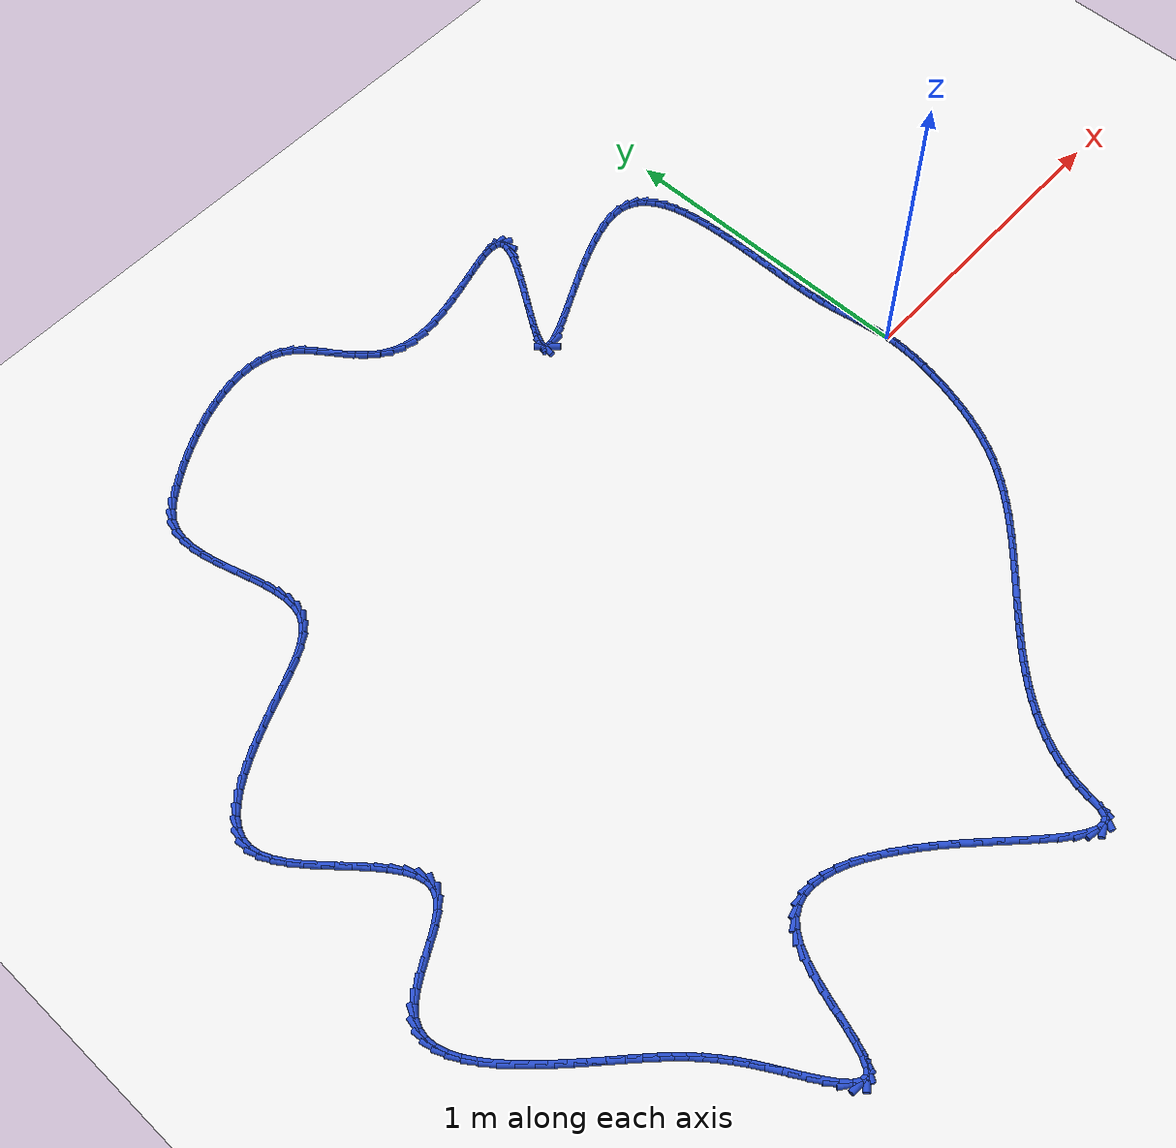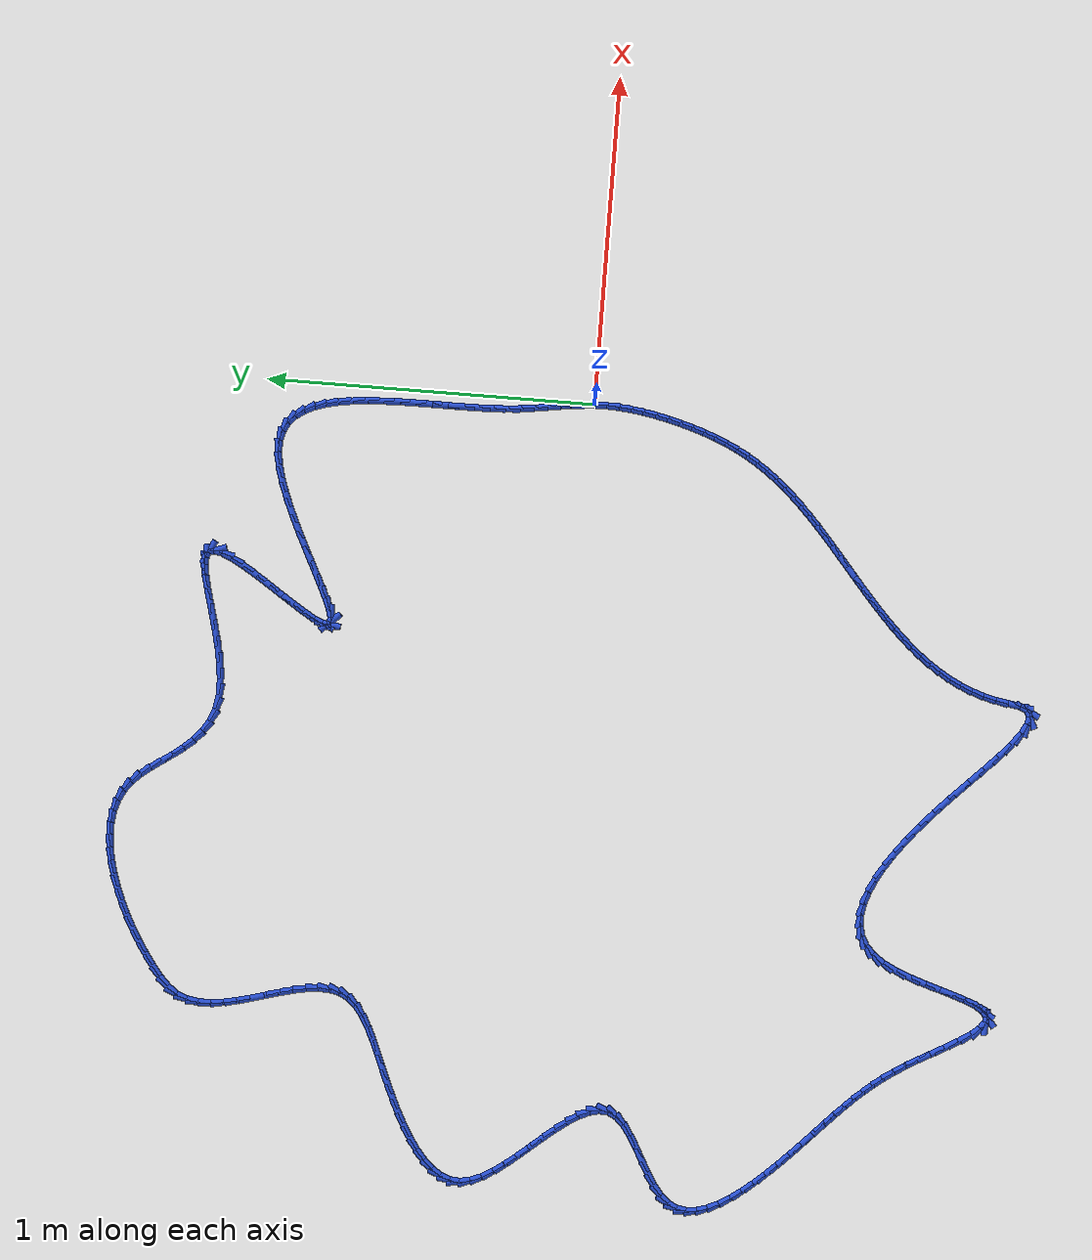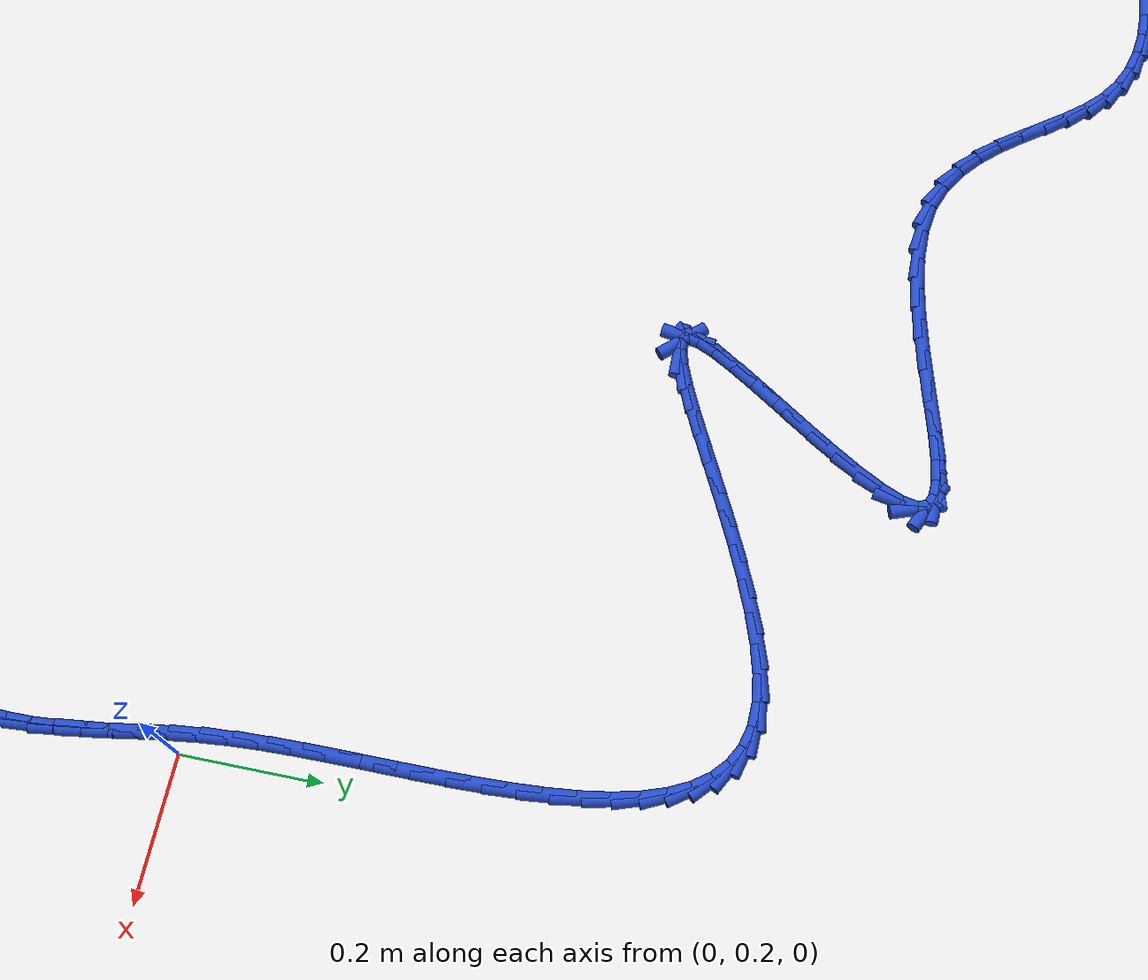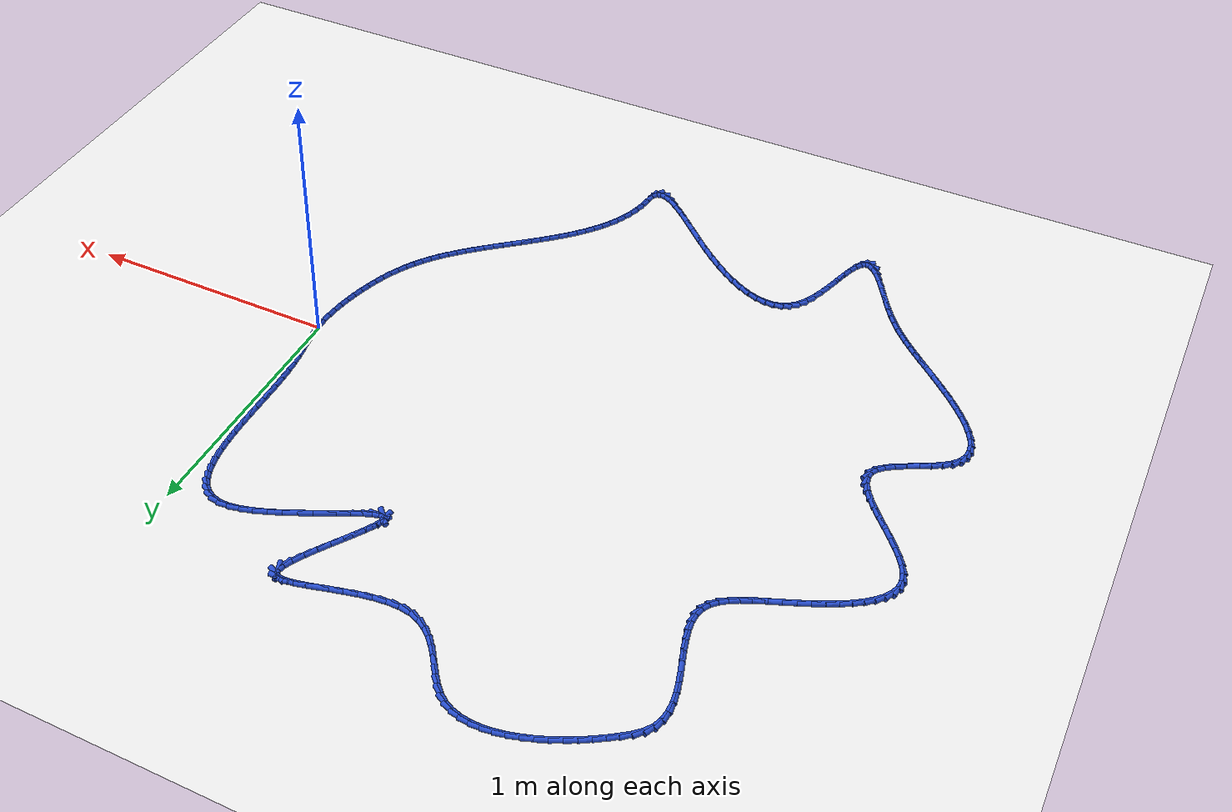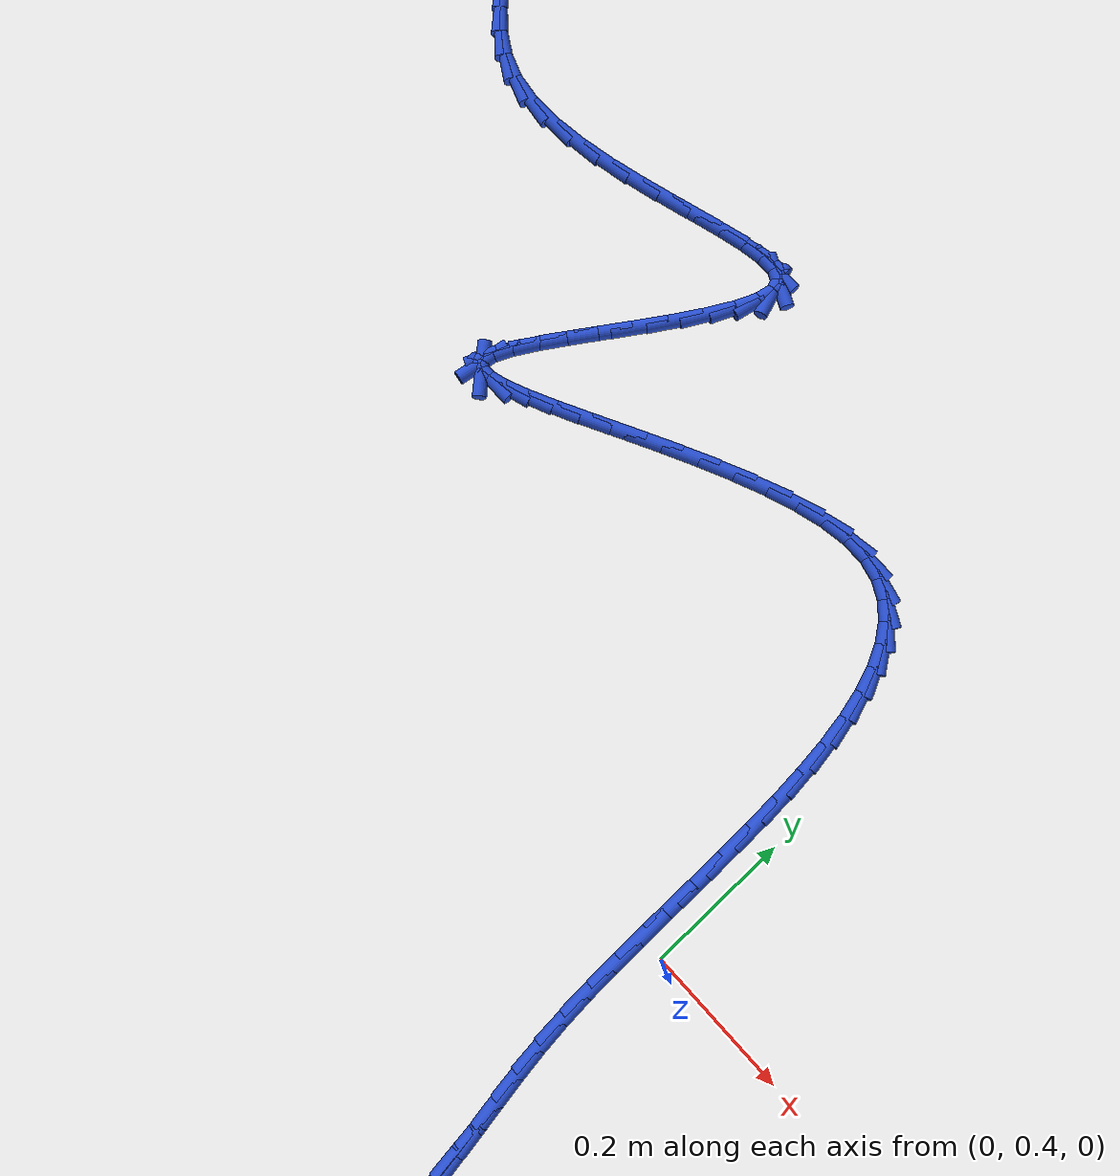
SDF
<sdf version="1.6">
 <world name="default">
  <light name="sun" type="directional">
   <pose>0 0 10 0 -0 0</pose>
   <diffuse>0.8 0.8 0.8 1</diffuse>
   <specular>0.2 0.2 0.2 1</specular>
   <attenuation>
    <range>1000</range>
    <constant>0.9</constant>
    <linear>0.01</linear>
    <quadratic>0.001</quadratic>
   </attenuation>
   <direction>-0.5 0.1 -0.9</direction>
  </light>
  <model name="ground_plane">
   <static>1</static>
   <link name="link">
    <collision name="collision">
     <geometry><plane><normal>0 0 1</normal><size>100 100</size></plane></geometry>
     <surface><friction><ode><mu>100</mu><mu2>50</mu2></ode></friction></surface>
    </collision>
    <visual name="visual">
     <cast_shadows>0</cast_shadows>
     <geometry><plane><normal>0 0 1</normal><size>100 100</size></plane></geometry>
     <material>
      <script><uri>file://media/materials/scripts/gazebo.material</uri><name>Gazebo/WhiteGlow</name></script>
     </material>
    </visual>
   </link>
  </model>
  <gravity>0 0 -9.8</gravity>
  <magnetic_field>6e-06 2.3e-05 -4.2e-05</magnetic_field>
  <atmosphere type="adiabatic"/>
  <physics name="default_physics" default="0" type="ode">
   <max_step_size>0.001</max_step_size>
   <real_time_factor>1</real_time_factor>
   <real_time_update_rate>1000</real_time_update_rate>
  </physics>
  <scene><ambient>0.4 0.4 0.4 1</ambient><background>0.7 0.7 0.7 1</background><shadows>1</shadows></scene>
  <spherical_coordinates>
   <surface_model>EARTH_WGS84</surface_model>
   <latitude_deg>0</latitude_deg>
   <longitude_deg>0</longitude_deg>
   <elevation>0</elevation>
   <heading_deg>0</heading_deg>
  </spherical_coordinates>
  <model name="line">
   <link name="link_0">
    <pose>1.0408340855860843e-17 6.938893903907228e-18 0.01 0 1.57 -1.500443968666849</pose>
    <collision name="collision">
     <geometry><cylinder><radius>0.01</radius><length>0.08</length></cylinder></geometry>
    </collision>
    <visual name="visual">
     <material>
      <script><name>Gazebo/Blue</name><uri>file://media/materials/scripts/gazebo.material</uri></script>
     </material>
     <geometry><cylinder><radius>0.01</radius><length>0.08</length></cylinder></geometry>
    </visual>
   </link>
   <link name="link_1">
    <pose>-0.0025369876689253705 0.03600164637563605 0.01 0 1.57 -1.4529405909059698</pose>
    <collision name="collision">
     <geometry><cylinder><radius>0.01</radius><length>0.08</length></cylinder></geometry>
    </collision>
    <visual name="visual">
     <material>
      <script><name>Gazebo/Blue</name><uri>file://media/materials/scripts/gazebo.material</uri></script>
     </material>
     <geometry><cylinder><radius>0.01</radius><length>0.08</length></cylinder></geometry>
    </visual>
   </link>
   <link name="link_2">
    <pose>-0.0067697475077727115 0.07174996183603236 0.01 0 1.57 -1.4236694929863785</pose>
    <collision name="collision">
     <geometry><cylinder><radius>0.01</radius><length>0.08</length></cylinder></geometry>
    </collision>
    <visual name="visual">
     <material>
      <script><name>Gazebo/Blue</name><uri>file://media/materials/scripts/gazebo.material</uri></script>
     </material>
     <geometry><cylinder><radius>0.01</radius><length>0.08</length></cylinder></geometry>
    </visual>
   </link>
   <link name="link_3">
    <pose>-0.012106916807119367 0.10776381108110997 0.01 0 1.57 -1.4131349505841373</pose>
    <collision name="collision">
     <geometry><cylinder><radius>0.01</radius><length>0.08</length></cylinder></geometry>
    </collision>
    <visual name="visual">
     <material>
      <script><name>Gazebo/Blue</name><uri>file://media/materials/scripts/gazebo.material</uri></script>
     </material>
     <geometry><cylinder><radius>0.01</radius><length>0.08</length></cylinder></geometry>
    </visual>
   </link>
   <link name="link_4">
    <pose>-0.017957132857542687 0.1445620588107898 0.01 0 1.57 -1.4204519951015675</pose>
    <collision name="collision">
     <geometry><cylinder><radius>0.01</radius><length>0.08</length></cylinder></geometry>
    </collision>
    <visual name="visual">
     <material>
      <script><name>Gazebo/Blue</name><uri>file://media/materials/scripts/gazebo.material</uri></script>
     </material>
     <geometry><cylinder><radius>0.01</radius><length>0.08</length></cylinder></geometry>
    </visual>
   </link>
   <link name="link_5">
    <pose>-0.02372903294962001 0.18266356972499284 0.01 0 1.57 -1.4436858492961933</pose>
    <collision name="collision">
     <geometry><cylinder><radius>0.01</radius><length>0.08</length></cylinder></geometry>
    </collision>
    <visual name="visual">
     <material>
      <script><name>Gazebo/Blue</name><uri>file://media/materials/scripts/gazebo.material</uri></script>
     </material>
     <geometry><cylinder><radius>0.01</radius><length>0.08</length></cylinder></geometry>
    </visual>
   </link>
   <link name="link_6">
    <pose>-0.028831254373928694 0.22258720852364006 0.01 0 1.57 -1.4799480751914387</pose>
    <collision name="collision">
     <geometry><cylinder><radius>0.01</radius><length>0.08</length></cylinder></geometry>
    </collision>
    <visual name="visual">
     <material>
      <script><name>Gazebo/Blue</name><uri>file://media/materials/scripts/gazebo.material</uri></script>
     </material>
     <geometry><cylinder><radius>0.01</radius><length>0.08</length></cylinder></geometry>
    </visual>
   </link>
   <link name="link_7">
    <pose>-0.03268069156678858 0.2648427387323173 0.01 0 1.57 -1.5174231341432383</pose>
    <collision name="collision">
     <geometry><cylinder><radius>0.01</radius><length>0.08</length></cylinder></geometry>
    </collision>
    <visual name="visual">
     <material>
      <script><name>Gazebo/Blue</name><uri>file://media/materials/scripts/gazebo.material</uri></script>
     </material>
     <geometry><cylinder><radius>0.01</radius><length>0.08</length></cylinder></geometry>
    </visual>
   </link>
   <link name="link_8">
    <pose>-0.03506795434964404 0.309528008067227 0.01 0 1.57 -1.5443436570944173</pose>
    <collision name="collision">
     <geometry><cylinder><radius>0.01</radius><length>0.08</length></cylinder></geometry>
    </collision>
    <visual name="visual">
     <material>
      <script><name>Gazebo/Blue</name><uri>file://media/materials/scripts/gazebo.material</uri></script>
     </material>
     <geometry><cylinder><radius>0.01</radius><length>0.08</length></cylinder></geometry>
    </visual>
   </link>
   <link name="link_9">
    <pose>-0.03630203405338728 0.35616949483476634 0.01 0 1.57 -1.5618940222247308</pose>
    <collision name="collision">
     <geometry><cylinder><radius>0.01</radius><length>0.08</length></cylinder></geometry>
    </collision>
    <visual name="visual">
     <material>
      <script><name>Gazebo/Blue</name><uri>file://media/materials/scripts/gazebo.material</uri></script>
     </material>
     <geometry><cylinder><radius>0.01</radius><length>0.08</length></cylinder></geometry>
    </visual>
   </link>
   <link name="link_10">
    <pose>-0.03673008700555676 0.4042516111965887 0.01 0 1.57 1.5701674907434413</pose>
    <collision name="collision">
     <geometry><cylinder><radius>0.01</radius><length>0.08</length></cylinder></geometry>
    </collision>
    <visual name="visual">
     <material>
      <script><name>Gazebo/Blue</name><uri>file://media/materials/scripts/gazebo.material</uri></script>
     </material>
     <geometry><cylinder><radius>0.01</radius><length>0.08</length></cylinder></geometry>
    </visual>
   </link>
   <link name="link_11">
    <pose>-0.03669926953369084 0.4532587693143473 0.01 0 1.57 1.5679120502884816</pose>
    <collision name="collision">
     <geometry><cylinder><radius>0.01</radius><length>0.08</length></cylinder></geometry>
    </collision>
    <visual name="visual">
     <material>
      <script><name>Gazebo/Blue</name><uri>file://media/materials/scripts/gazebo.material</uri></script>
     </material>
     <geometry><cylinder><radius>0.01</radius><length>0.08</length></cylinder></geometry>
    </visual>
   </link>
   <link name="link_12">
    <pose>-0.03655673796532798 0.5026753813496957 0.01 0 1.57 -1.5689121318675527</pose>
    <collision name="collision">
     <geometry><cylinder><radius>0.01</radius><length>0.08</length></cylinder></geometry>
    </collision>
    <visual name="visual">
     <material>
      <script><name>Gazebo/Blue</name><uri>file://media/materials/scripts/gazebo.material</uri></script>
     </material>
     <geometry><cylinder><radius>0.01</radius><length>0.08</length></cylinder></geometry>
    </visual>
   </link>
   <link name="link_13">
    <pose>-0.03664964862800661 0.5519858594642875 0.01 0 1.57 -1.5569231878158445</pose>
    <collision name="collision">
     <geometry><cylinder><radius>0.01</radius><length>0.08</length></cylinder></geometry>
    </collision>
    <visual name="visual">
     <material>
      <script><name>Gazebo/Blue</name><uri>file://media/materials/scripts/gazebo.material</uri></script>
     </material>
     <geometry><cylinder><radius>0.01</radius><length>0.08</length></cylinder></geometry>
    </visual>
   </link>
   <link name="link_14">
    <pose>-0.03732515784926514 0.6006746158197754 0.01 0 1.57 -1.5370506717471328</pose>
    <collision name="collision">
     <geometry><cylinder><radius>0.01</radius><length>0.08</length></cylinder></geometry>
    </collision>
    <visual name="visual">
     <material>
      <script><name>Gazebo/Blue</name><uri>file://media/materials/scripts/gazebo.material</uri></script>
     </material>
     <geometry><cylinder><radius>0.01</radius><length>0.08</length></cylinder></geometry>
    </visual>
   </link>
   <link name="link_15">
    <pose>-0.03893042195664197 0.6482260625778136 0.01 0 1.57 -1.5080841927181026</pose>
    <collision name="collision">
     <geometry><cylinder><radius>0.01</radius><length>0.08</length></cylinder></geometry>
    </collision>
    <visual name="visual">
     <material>
      <script><name>Gazebo/Blue</name><uri>file://media/materials/scripts/gazebo.material</uri></script>
     </material>
     <geometry><cylinder><radius>0.01</radius><length>0.08</length></cylinder></geometry>
    </visual>
   </link>
   <link name="link_16">
    <pose>-0.04181259727767554 0.6941246119000548 0.01 0 1.57 -1.4681119663431792</pose>
    <collision name="collision">
     <geometry><cylinder><radius>0.01</radius><length>0.08</length></cylinder></geometry>
    </collision>
    <visual name="visual">
     <material>
      <script><name>Gazebo/Blue</name><uri>file://media/materials/scripts/gazebo.material</uri></script>
     </material>
     <geometry><cylinder><radius>0.01</radius><length>0.08</length></cylinder></geometry>
    </visual>
   </link>
   <link name="link_17">
    <pose>-0.046318840139904276 0.7378546759481527 0.01 0 1.57 -1.4142771526820412</pose>
    <collision name="collision">
     <geometry><cylinder><radius>0.01</radius><length>0.08</length></cylinder></geometry>
    </collision>
    <visual name="visual">
     <material>
      <script><name>Gazebo/Blue</name><uri>file://media/materials/scripts/gazebo.material</uri></script>
     </material>
     <geometry><cylinder><radius>0.01</radius><length>0.08</length></cylinder></geometry>
    </visual>
   </link>
   <link name="link_18">
    <pose>-0.052796306870866595 0.7789006668837611 0.01 0 1.57 -1.3424406977237866</pose>
    <collision name="collision">
     <geometry><cylinder><radius>0.01</radius><length>0.08</length></cylinder></geometry>
    </collision>
    <visual name="visual">
     <material>
      <script><name>Gazebo/Blue</name><uri>file://media/materials/scripts/gazebo.material</uri></script>
     </material>
     <geometry><cylinder><radius>0.01</radius><length>0.08</length></cylinder></geometry>
    </visual>
   </link>
   <link name="link_19">
    <pose>-0.061592153798100825 0.8167469968685326 0.01 0 1.57 -1.2468230367276674</pose>
    <collision name="collision">
     <geometry><cylinder><radius>0.01</radius><length>0.08</length></cylinder></geometry>
    </collision>
    <visual name="visual">
     <material>
      <script><name>Gazebo/Blue</name><uri>file://media/materials/scripts/gazebo.material</uri></script>
     </material>
     <geometry><cylinder><radius>0.01</radius><length>0.08</length></cylinder></geometry>
    </visual>
   </link>
   <link name="link_20">
    <pose>-0.07305353724914557 0.8508780780641211 0.01 0 1.57 -1.1199665621676775</pose>
    <collision name="collision">
     <geometry><cylinder><radius>0.01</radius><length>0.08</length></cylinder></geometry>
    </collision>
    <visual name="visual">
     <material>
      <script><name>Gazebo/Blue</name><uri>file://media/materials/scripts/gazebo.material</uri></script>
     </material>
     <geometry><cylinder><radius>0.01</radius><length>0.08</length></cylinder></geometry>
    </visual>
   </link>
   <link name="link_21">
    <pose>-0.08752761355153912 0.8807783226321797 0.01 0 1.57 -0.9540591162776518</pose>
    <collision name="collision">
     <geometry><cylinder><radius>0.01</radius><length>0.08</length></cylinder></geometry>
    </collision>
    <visual name="visual">
     <material>
      <script><name>Gazebo/Blue</name><uri>file://media/materials/scripts/gazebo.material</uri></script>
     </material>
     <geometry><cylinder><radius>0.01</radius><length>0.08</length></cylinder></geometry>
    </visual>
   </link>
   <link name="link_22">
    <pose>-0.10536153903281986 0.9059321427343617 0.01 0 1.57 -0.7456167441606393</pose>
    <collision name="collision">
     <geometry><cylinder><radius>0.01</radius><length>0.08</length></cylinder></geometry>
    </collision>
    <visual name="visual">
     <material>
      <script><name>Gazebo/Blue</name><uri>file://media/materials/scripts/gazebo.material</uri></script>
     </material>
     <geometry><cylinder><radius>0.01</radius><length>0.08</length></cylinder></geometry>
    </visual>
   </link>
   <link name="link_23">
    <pose>-0.12690247002052626 0.9258239505323209 0.01 0 1.57 -0.5039495929432688</pose>
    <collision name="collision">
     <geometry><cylinder><radius>0.01</radius><length>0.08</length></cylinder></geometry>
    </collision>
    <visual name="visual">
     <material>
      <script><name>Gazebo/Blue</name><uri>file://media/materials/scripts/gazebo.material</uri></script>
     </material>
     <geometry><cylinder><radius>0.01</radius><length>0.08</length></cylinder></geometry>
    </visual>
   </link>
   <link name="link_24">
    <pose>-0.15249756284219687 0.9399381581877106 0.01 0 1.57 -0.25505344413963066</pose>
    <collision name="collision">
     <geometry><cylinder><radius>0.01</radius><length>0.08</length></cylinder></geometry>
    </collision>
    <visual name="visual">
     <material>
      <script><name>Gazebo/Blue</name><uri>file://media/materials/scripts/gazebo.material</uri></script>
     </material>
     <geometry><cylinder><radius>0.01</radius><length>0.08</length></cylinder></geometry>
    </visual>
   </link>
   <link name="link_25">
    <pose>-0.18249397382536997 0.9477591778621841 0.01 0 1.57 -0.029323682449118125</pose>
    <collision name="collision">
     <geometry><cylinder><radius>0.01</radius><length>0.08</length></cylinder></geometry>
    </collision>
    <visual name="visual">
     <material>
      <script><name>Gazebo/Blue</name><uri>file://media/materials/scripts/gazebo.material</uri></script>
     </material>
     <geometry><cylinder><radius>0.01</radius><length>0.08</length></cylinder></geometry>
    </visual>
   </link>
   <link name="link_26">
    <pose>-0.21723323922063867 0.9487781531308197 0.01 0 1.57 0.14458358745321898</pose>
    <collision name="collision">
     <geometry><cylinder><radius>0.01</radius><length>0.08</length></cylinder></geometry>
    </collision>
    <visual name="visual">
     <material>
      <script><name>Gazebo/Blue</name><uri>file://media/materials/scripts/gazebo.material</uri></script>
     </material>
     <geometry><cylinder><radius>0.01</radius><length>0.08</length></cylinder></geometry>
    </visual>
   </link>
   <link name="link_27">
    <pose>-0.25658774041202315 0.9430481549938726 0.01 0 1.57 0.2600713470197988</pose>
    <collision name="collision">
     <geometry><cylinder><radius>0.01</radius><length>0.08</length></cylinder></geometry>
    </collision>
    <visual name="visual">
     <material>
      <script><name>Gazebo/Blue</name><uri>file://media/materials/scripts/gazebo.material</uri></script>
     </material>
     <geometry><cylinder><radius>0.01</radius><length>0.08</length></cylinder></geometry>
    </visual>
   </link>
   <link name="link_28">
    <pose>-0.29961452426344165 0.9315988164787293 0.01 0 1.57 0.3377523772484208</pose>
    <collision name="collision">
     <geometry><cylinder><radius>0.01</radius><length>0.08</length></cylinder></geometry>
    </collision>
    <visual name="visual">
     <material>
      <script><name>Gazebo/Blue</name><uri>file://media/materials/scripts/gazebo.material</uri></script>
     </material>
     <geometry><cylinder><radius>0.01</radius><length>0.08</length></cylinder></geometry>
    </visual>
   </link>
   <link name="link_29">
    <pose>-0.34528908086877824 0.9155574547445142 0.01 0 1.57 0.3911581954063963</pose>
    <collision name="collision">
     <geometry><cylinder><radius>0.01</radius><length>0.08</length></cylinder></geometry>
    </collision>
    <visual name="visual">
     <material>
      <script><name>Gazebo/Blue</name><uri>file://media/materials/scripts/gazebo.material</uri></script>
     </material>
     <geometry><cylinder><radius>0.01</radius><length>0.08</length></cylinder></geometry>
    </visual>
   </link>
   <link name="link_30">
    <pose>-0.39258690032191607 0.8960513869503501 0.01 0 1.57 0.42787759025588906</pose>
    <collision name="collision">
     <geometry><cylinder><radius>0.01</radius><length>0.08</length></cylinder></geometry>
    </collision>
    <visual name="visual">
     <material>
      <script><name>Gazebo/Blue</name><uri>file://media/materials/scripts/gazebo.material</uri></script>
     </material>
     <geometry><cylinder><radius>0.01</radius><length>0.08</length></cylinder></geometry>
    </visual>
   </link>
   <link name="link_31">
    <pose>-0.44048347271673927 0.8742079302553609 0.01 0 1.57 0.45209037355442655</pose>
    <collision name="collision">
     <geometry><cylinder><radius>0.01</radius><length>0.08</length></cylinder></geometry>
    </collision>
    <visual name="visual">
     <material>
      <script><name>Gazebo/Blue</name><uri>file://media/materials/scripts/gazebo.material</uri></script>
     </material>
     <geometry><cylinder><radius>0.01</radius><length>0.08</length></cylinder></geometry>
    </visual>
   </link>
   <link name="link_32">
    <pose>-0.4879542881471314 0.8511544018186704 0.01 0 1.57 0.4658356868698599</pose>
    <collision name="collision">
     <geometry><cylinder><radius>0.01</radius><length>0.08</length></cylinder></geometry>
    </collision>
    <visual name="visual">
     <material>
      <script><name>Gazebo/Blue</name><uri>file://media/materials/scripts/gazebo.material</uri></script>
     </material>
     <geometry><cylinder><radius>0.01</radius><length>0.08</length></cylinder></geometry>
    </visual>
   </link>
   <link name="link_33">
    <pose>-0.5339748367069761 0.8280181187994025 0.01 0 1.57 0.4694878983341049</pose>
    <collision name="collision">
     <geometry><cylinder><radius>0.01</radius><length>0.08</length></cylinder></geometry>
    </collision>
    <visual name="visual">
     <material>
      <script><name>Gazebo/Blue</name><uri>file://media/materials/scripts/gazebo.material</uri></script>
     </material>
     <geometry><cylinder><radius>0.01</radius><length>0.08</length></cylinder></geometry>
    </visual>
   </link>
   <link name="link_34">
    <pose>-0.5775206084901567 0.80592639835668 0.01 0 1.57 0.4615798399852503</pose>
    <collision name="collision">
     <geometry><cylinder><radius>0.01</radius><length>0.08</length></cylinder></geometry>
    </collision>
    <visual name="visual">
     <material>
      <script><name>Gazebo/Blue</name><uri>file://media/materials/scripts/gazebo.material</uri></script>
     </material>
     <geometry><cylinder><radius>0.01</radius><length>0.08</length></cylinder></geometry>
    </visual>
   </link>
   <link name="link_35">
    <pose>-0.6175670935905574 0.7860065576496273 0.01 0 1.57 0.43762970539203705</pose>
    <collision name="collision">
     <geometry><cylinder><radius>0.01</radius><length>0.08</length></cylinder></geometry>
    </collision>
    <visual name="visual">
     <material>
      <script><name>Gazebo/Blue</name><uri>file://media/materials/scripts/gazebo.material</uri></script>
     </material>
     <geometry><cylinder><radius>0.01</radius><length>0.08</length></cylinder></geometry>
    </visual>
   </link>
   <link name="link_36">
    <pose>-0.6530897821020614 0.7693859138373679 0.01 0 1.57 0.38637044259434405</pose>
    <collision name="collision">
     <geometry><cylinder><radius>0.01</radius><length>0.08</length></cylinder></geometry>
    </collision>
    <visual name="visual">
     <material>
      <script><name>Gazebo/Blue</name><uri>file://media/materials/scripts/gazebo.material</uri></script>
     </material>
     <geometry><cylinder><radius>0.01</radius><length>0.08</length></cylinder></geometry>
    </visual>
   </link>
   <link name="link_37">
    <pose>-0.6830641641185524 0.7571917840790253 0.01 0 1.57 0.2764868054256121</pose>
    <collision name="collision">
     <geometry><cylinder><radius>0.01</radius><length>0.08</length></cylinder></geometry>
    </collision>
    <visual name="visual">
     <material>
      <script><name>Gazebo/Blue</name><uri>file://media/materials/scripts/gazebo.material</uri></script>
     </material>
     <geometry><cylinder><radius>0.01</radius><length>0.08</length></cylinder></geometry>
    </visual>
   </link>
   <link name="link_38">
    <pose>-0.7064657297339147 0.7505514855337232 0.01 0 1.57 -0.0025847328109349192</pose>
    <collision name="collision">
     <geometry><cylinder><radius>0.01</radius><length>0.08</length></cylinder></geometry>
    </collision>
    <visual name="visual">
     <material>
      <script><name>Gazebo/Blue</name><uri>file://media/materials/scripts/gazebo.material</uri></script>
     </material>
     <geometry><cylinder><radius>0.01</radius><length>0.08</length></cylinder></geometry>
    </visual>
   </link>
   <link name="link_39">
    <pose>-0.7222699690420312 0.7505923353605852 0.01 0 1.57 -0.8297360873263988</pose>
    <collision name="collision">
     <geometry><cylinder><radius>0.01</radius><length>0.08</length></cylinder></geometry>
    </collision>
    <visual name="visual">
     <material>
      <script><name>Gazebo/Blue</name><uri>file://media/materials/scripts/gazebo.material</uri></script>
     </material>
     <geometry><cylinder><radius>0.01</radius><length>0.08</length></cylinder></geometry>
    </visual>
   </link>
   <link name="link_40">
    <pose>-0.7294523721367859 0.758441650718735 0.01 0 1.57 1.431003141177874</pose>
    <collision name="collision">
     <geometry><cylinder><radius>0.01</radius><length>0.08</length></cylinder></geometry>
    </collision>
    <visual name="visual">
     <material>
      <script><name>Gazebo/Blue</name><uri>file://media/materials/scripts/gazebo.material</uri></script>
     </material>
     <geometry><cylinder><radius>0.01</radius><length>0.08</length></cylinder></geometry>
    </visual>
   </link>
   <link name="link_41">
    <pose>-0.7271064222086081 0.7751137678074754 0.01 0 1.57 1.1502650298836266</pose>
    <collision name="collision">
     <geometry><cylinder><radius>0.01</radius><length>0.08</length></cylinder></geometry>
    </collision>
    <visual name="visual">
     <material>
      <script><name>Gazebo/Blue</name><uri>file://media/materials/scripts/gazebo.material</uri></script>
     </material>
     <geometry><cylinder><radius>0.01</radius><length>0.08</length></cylinder></geometry>
    </visual>
   </link>
   <link name="link_42">
    <pose>-0.7159444178381522 0.8000729718323228 0.01 0 1.57 1.0506521598981609</pose>
    <collision name="collision">
     <geometry><cylinder><radius>0.01</radius><length>0.08</length></cylinder></geometry>
    </collision>
    <visual name="visual">
     <material>
      <script><name>Gazebo/Blue</name><uri>file://media/materials/scripts/gazebo.material</uri></script>
     </material>
     <geometry><cylinder><radius>0.01</radius><length>0.08</length></cylinder></geometry>
    </visual>
   </link>
   <link name="link_43">
    <pose>-0.6978538093017287 0.8316583146555109 0.01 0 1.57 1.0067605238913357</pose>
    <collision name="collision">
     <geometry><cylinder><radius>0.01</radius><length>0.08</length></cylinder></geometry>
    </collision>
    <visual name="visual">
     <material>
      <script><name>Gazebo/Blue</name><uri>file://media/materials/scripts/gazebo.material</uri></script>
     </material>
     <geometry><cylinder><radius>0.01</radius><length>0.08</length></cylinder></geometry>
    </visual>
   </link>
   <link name="link_44">
    <pose>-0.6747484437576611 0.8681835725498236 0.01 0 1.57 0.9882613577577913</pose>
    <collision name="collision">
     <geometry><cylinder><radius>0.01</radius><length>0.08</length></cylinder></geometry>
    </collision>
    <visual name="visual">
     <material>
      <script><name>Gazebo/Blue</name><uri>file://media/materials/scripts/gazebo.material</uri></script>
     </material>
     <geometry><cylinder><radius>0.01</radius><length>0.08</length></cylinder></geometry>
    </visual>
   </link>
   <link name="link_45">
    <pose>-0.6485421683642731 0.9079625217880456 0.01 0 1.57 0.985661417324409</pose>
    <collision name="collision">
     <geometry><cylinder><radius>0.01</radius><length>0.08</length></cylinder></geometry>
    </collision>
    <visual name="visual">
     <material>
      <script><name>Gazebo/Blue</name><uri>file://media/materials/scripts/gazebo.material</uri></script>
     </material>
     <geometry><cylinder><radius>0.01</radius><length>0.08</length></cylinder></geometry>
    </visual>
   </link>
   <link name="link_46">
    <pose>-0.6211488302798881 0.9493089386429608 0.01 0 1.57 0.9966653613283086</pose>
    <collision name="collision">
     <geometry><cylinder><radius>0.01</radius><length>0.08</length></cylinder></geometry>
    </collision>
    <visual name="visual">
     <material>
      <script><name>Gazebo/Blue</name><uri>file://media/materials/scripts/gazebo.material</uri></script>
     </material>
     <geometry><cylinder><radius>0.01</radius><length>0.08</length></cylinder></geometry>
    </visual>
   </link>
   <link name="link_47">
    <pose>-0.5944822766628304 0.9905365993873536 0.01 0 1.57 1.0234615270394165</pose>
    <collision name="collision">
     <geometry><cylinder><radius>0.01</radius><length>0.08</length></cylinder></geometry>
    </collision>
    <visual name="visual">
     <material>
      <script><name>Gazebo/Blue</name><uri>file://media/materials/scripts/gazebo.material</uri></script>
     </material>
     <geometry><cylinder><radius>0.01</radius><length>0.08</length></cylinder></geometry>
    </visual>
   </link>
   <link name="link_48">
    <pose>-0.570456354671423 1.029959280294008 0.01 0 1.57 1.0741894098396336</pose>
    <collision name="collision">
     <geometry><cylinder><radius>0.01</radius><length>0.08</length></cylinder></geometry>
    </collision>
    <visual name="visual">
     <material>
      <script><name>Gazebo/Blue</name><uri>file://media/materials/scripts/gazebo.material</uri></script>
     </material>
     <geometry><cylinder><radius>0.01</radius><length>0.08</length></cylinder></geometry>
    </visual>
   </link>
   <link name="link_49">
    <pose>-0.5509849114639899 1.0658907576357088 0.01 0 1.57 1.1707821631627116</pose>
    <collision name="collision">
     <geometry><cylinder><radius>0.01</radius><length>0.08</length></cylinder></geometry>
    </collision>
    <visual name="visual">
     <material>
      <script><name>Gazebo/Blue</name><uri>file://media/materials/scripts/gazebo.material</uri></script>
     </material>
     <geometry><cylinder><radius>0.01</radius><length>0.08</length></cylinder></geometry>
    </visual>
   </link>
   <link name="link_50">
    <pose>-0.5379817941988547 1.0966448076852395 0.01 0 1.57 1.3797330720430225</pose>
    <collision name="collision">
     <geometry><cylinder><radius>0.01</radius><length>0.08</length></cylinder></geometry>
    </collision>
    <visual name="visual">
     <material>
      <script><name>Gazebo/Blue</name><uri>file://media/materials/scripts/gazebo.material</uri></script>
     </material>
     <geometry><cylinder><radius>0.01</radius><length>0.08</length></cylinder></geometry>
    </visual>
   </link>
   <link name="link_51">
    <pose>-0.533360850034341 1.1205352067153849 0.01 0 1.57 -1.2338911238755252</pose>
    <collision name="collision">
     <geometry><cylinder><radius>0.01</radius><length>0.08</length></cylinder></geometry>
    </collision>
    <visual name="visual">
     <material>
      <script><name>Gazebo/Blue</name><uri>file://media/materials/scripts/gazebo.material</uri></script>
     </material>
     <geometry><cylinder><radius>0.01</radius><length>0.08</length></cylinder></geometry>
    </visual>
   </link>
   <link name="link_52">
    <pose>-0.538809367825531 1.1360909057929303 0.01 0 1.57 -0.46155128257823674</pose>
    <collision name="collision">
     <geometry><cylinder><radius>0.01</radius><length>0.08</length></cylinder></geometry>
    </collision>
    <visual name="visual">
     <material>
      <script><name>Gazebo/Blue</name><uri>file://media/materials/scripts/gazebo.material</uri></script>
     </material>
     <geometry><cylinder><radius>0.01</radius><length>0.08</length></cylinder></geometry>
    </visual>
   </link>
   <link name="link_53">
    <pose>-0.5540744977054676 1.1436835116890747 0.01 0 1.57 -0.03928888125267057</pose>
    <collision name="collision">
     <geometry><cylinder><radius>0.01</radius><length>0.08</length></cylinder></geometry>
    </collision>
    <visual name="visual">
     <material>
      <script><name>Gazebo/Blue</name><uri>file://media/materials/scripts/gazebo.material</uri></script>
     </material>
     <geometry><cylinder><radius>0.01</radius><length>0.08</length></cylinder></geometry>
    </visual>
   </link>
   <link name="link_54">
    <pose>-0.5779177281899871 1.144620767844488 0.01 0 1.57 0.14030613843671622</pose>
    <collision name="collision">
     <geometry><cylinder><radius>0.01</radius><length>0.08</length></cylinder></geometry>
    </collision>
    <visual name="visual">
     <material>
      <script><name>Gazebo/Blue</name><uri>file://media/materials/scripts/gazebo.material</uri></script>
     </material>
     <geometry><cylinder><radius>0.01</radius><length>0.08</length></cylinder></geometry>
    </visual>
   </link>
   <link name="link_55">
    <pose>-0.6090927905944125 1.140217785136826 0.01 0 1.57 0.2224501259089498</pose>
    <collision name="collision">
     <geometry><cylinder><radius>0.01</radius><length>0.08</length></cylinder></geometry>
    </collision>
    <visual name="visual">
     <material>
      <script><name>Gazebo/Blue</name><uri>file://media/materials/scripts/gazebo.material</uri></script>
     </material>
     <geometry><cylinder><radius>0.01</radius><length>0.08</length></cylinder></geometry>
    </visual>
   </link>
   <link name="link_56">
    <pose>-0.6463534162340662 1.1317896744437455 0.01 0 1.57 0.25863839580004233</pose>
    <collision name="collision">
     <geometry><cylinder><radius>0.01</radius><length>0.08</length></cylinder></geometry>
    </collision>
    <visual name="visual">
     <material>
      <script><name>Gazebo/Blue</name><uri>file://media/materials/scripts/gazebo.material</uri></script>
     </material>
     <geometry><cylinder><radius>0.01</radius><length>0.08</length></cylinder></geometry>
    </visual>
   </link>
   <link name="link_57">
    <pose>-0.6884533364242709 1.1206515466429015 0.01 0 1.57 0.26770429717890715</pose>
    <collision name="collision">
     <geometry><cylinder><radius>0.01</radius><length>0.08</length></cylinder></geometry>
    </collision>
    <visual name="visual">
     <material>
      <script><name>Gazebo/Blue</name><uri>file://media/materials/scripts/gazebo.material</uri></script>
     </material>
     <geometry><cylinder><radius>0.01</radius><length>0.08</length></cylinder></geometry>
    </visual>
   </link>
   <link name="link_58">
    <pose>-0.734146282480349 1.10811851261195 0.01 0 1.57 0.2567552098267681</pose>
    <collision name="collision">
     <geometry><cylinder><radius>0.01</radius><length>0.08</length></cylinder></geometry>
    </collision>
    <visual name="visual">
     <material>
      <script><name>Gazebo/Blue</name><uri>file://media/materials/scripts/gazebo.material</uri></script>
     </material>
     <geometry><cylinder><radius>0.01</radius><length>0.08</length></cylinder></geometry>
    </visual>
   </link>
   <link name="link_59">
    <pose>-0.7821859857176232 1.0955056832285477 0.01 0 1.57 0.22752267779796073</pose>
    <collision name="collision">
     <geometry><cylinder><radius>0.01</radius><length>0.08</length></cylinder></geometry>
    </collision>
    <visual name="visual">
     <material>
      <script><name>Gazebo/Blue</name><uri>file://media/materials/scripts/gazebo.material</uri></script>
     </material>
     <geometry><cylinder><radius>0.01</radius><length>0.08</length></cylinder></geometry>
    </visual>
   </link>
   <link name="link_60">
    <pose>-0.8313261774514161 1.0841281693703504 0.01 0 1.57 0.1782529392411769</pose>
    <collision name="collision">
     <geometry><cylinder><radius>0.01</radius><length>0.08</length></cylinder></geometry>
    </collision>
    <visual name="visual">
     <material>
      <script><name>Gazebo/Blue</name><uri>file://media/materials/scripts/gazebo.material</uri></script>
     </material>
     <geometry><cylinder><radius>0.01</radius><length>0.08</length></cylinder></geometry>
    </visual>
   </link>
   <link name="link_61">
    <pose>-0.8803205889970505 1.075301081915013 0.01 0 1.57 0.10385407735832532</pose>
    <collision name="collision">
     <geometry><cylinder><radius>0.01</radius><length>0.08</length></cylinder></geometry>
    </collision>
    <visual name="visual">
     <material>
      <script><name>Gazebo/Blue</name><uri>file://media/materials/scripts/gazebo.material</uri></script>
     </material>
     <geometry><cylinder><radius>0.01</radius><length>0.08</length></cylinder></geometry>
    </visual>
   </link>
   <link name="link_62">
    <pose>-0.9279229516698488 1.070339531740193 0.01 0 1.57 -0.00487269881432938</pose>
    <collision name="collision">
     <geometry><cylinder><radius>0.01</radius><length>0.08</length></cylinder></geometry>
    </collision>
    <visual name="visual">
     <material>
      <script><name>Gazebo/Blue</name><uri>file://media/materials/scripts/gazebo.material</uri></script>
     </material>
     <geometry><cylinder><radius>0.01</radius><length>0.08</length></cylinder></geometry>
    </visual>
   </link>
   <link name="link_63">
    <pose>-0.9728869967851337 1.070558629723545 0.01 0 1.57 -0.16198518433022618</pose>
    <collision name="collision">
     <geometry><cylinder><radius>0.01</radius><length>0.08</length></cylinder></geometry>
    </collision>
    <visual name="visual">
     <material>
      <script><name>Gazebo/Blue</name><uri>file://media/materials/scripts/gazebo.material</uri></script>
     </material>
     <geometry><cylinder><radius>0.01</radius><length>0.08</length></cylinder></geometry>
    </visual>
   </link>
   <link name="link_64">
    <pose>-1.0139676473515455 1.0772719064512235 0.01 0 1.57 -0.36381109437509324</pose>
    <collision name="collision">
     <geometry><cylinder><radius>0.01</radius><length>0.08</length></cylinder></geometry>
    </collision>
    <visual name="visual">
     <material>
      <script><name>Gazebo/Blue</name><uri>file://media/materials/scripts/gazebo.material</uri></script>
     </material>
     <geometry><cylinder><radius>0.01</radius><length>0.08</length></cylinder></geometry>
    </visual>
   </link>
   <link name="link_65">
    <pose>-1.0504071736064682 1.0911466266686969 0.01 0 1.57 -0.5562363748965382</pose>
    <collision name="collision">
     <geometry><cylinder><radius>0.01</radius><length>0.08</length></cylinder></geometry>
    </collision>
    <visual name="visual">
     <material>
      <script><name>Gazebo/Blue</name><uri>file://media/materials/scripts/gazebo.material</uri></script>
     </material>
     <geometry><cylinder><radius>0.01</radius><length>0.08</length></cylinder></geometry>
    </visual>
   </link>
   <link name="link_66">
    <pose>-1.082682493502889 1.1112128022618362 0.01 0 1.57 -0.7158559226145127</pose>
    <collision name="collision">
     <geometry><cylinder><radius>0.01</radius><length>0.08</length></cylinder></geometry>
    </collision>
    <visual name="visual">
     <material>
      <script><name>Gazebo/Blue</name><uri>file://media/materials/scripts/gazebo.material</uri></script>
     </material>
     <geometry><cylinder><radius>0.01</radius><length>0.08</length></cylinder></geometry>
    </visual>
   </link>
   <link name="link_67">
    <pose>-1.1114630903045932 1.1362450863596958 0.01 0 1.57 -0.836837689466625</pose>
    <collision name="collision">
     <geometry><cylinder><radius>0.01</radius><length>0.08</length></cylinder></geometry>
    </collision>
    <visual name="visual">
     <material>
      <script><name>Gazebo/Blue</name><uri>file://media/materials/scripts/gazebo.material</uri></script>
     </material>
     <geometry><cylinder><radius>0.01</radius><length>0.08</length></cylinder></geometry>
    </visual>
   </link>
   <link name="link_68">
    <pose>-1.1374184472753661 1.1650181320913315 0.01 0 1.57 -0.9200407580891101</pose>
    <collision name="collision">
     <geometry><cylinder><radius>0.01</radius><length>0.08</length></cylinder></geometry>
    </collision>
    <visual name="visual">
     <material>
      <script><name>Gazebo/Blue</name><uri>file://media/materials/scripts/gazebo.material</uri></script>
     </material>
     <geometry><cylinder><radius>0.01</radius><length>0.08</length></cylinder></geometry>
    </visual>
   </link>
   <link name="link_69">
    <pose>-1.1612311938498465 1.1962931923433506 0.01 0 1.57 -0.9620130884238275</pose>
    <collision name="collision">
     <geometry><cylinder><radius>0.01</radius><length>0.08</length></cylinder></geometry>
    </collision>
    <visual name="visual">
     <material>
      <script><name>Gazebo/Blue</name><uri>file://media/materials/scripts/gazebo.material</uri></script>
     </material>
     <geometry><cylinder><radius>0.01</radius><length>0.08</length></cylinder></geometry>
    </visual>
   </link>
   <link name="link_70">
    <pose>-1.183776878643369 1.22863487233799 0.01 0 1.57 -0.9595573245800335</pose>
    <collision name="collision">
     <geometry><cylinder><radius>0.01</radius><length>0.08</length></cylinder></geometry>
    </collision>
    <visual name="visual">
     <material>
      <script><name>Gazebo/Blue</name><uri>file://media/materials/scripts/gazebo.material</uri></script>
     </material>
     <geometry><cylinder><radius>0.01</radius><length>0.08</length></cylinder></geometry>
    </visual>
   </link>
   <link name="link_71">
    <pose>-1.206077646761988 1.2604583475860298 0.01 0 1.57 -0.9104106159157307</pose>
    <collision name="collision">
     <geometry><cylinder><radius>0.01</radius><length>0.08</length></cylinder></geometry>
    </collision>
    <visual name="visual">
     <material>
      <script><name>Gazebo/Blue</name><uri>file://media/materials/scripts/gazebo.material</uri></script>
     </material>
     <geometry><cylinder><radius>0.01</radius><length>0.08</length></cylinder></geometry>
    </visual>
   </link>
   <link name="link_72">
    <pose>-1.2291593054186412 1.2901750607150704 0.01 0 1.57 -0.8076502901971765</pose>
    <collision name="collision">
     <geometry><cylinder><radius>0.01</radius><length>0.08</length></cylinder></geometry>
    </collision>
    <visual name="visual">
     <material>
      <script><name>Gazebo/Blue</name><uri>file://media/materials/scripts/gazebo.material</uri></script>
     </material>
     <geometry><cylinder><radius>0.01</radius><length>0.08</length></cylinder></geometry>
    </visual>
   </link>
   <link name="link_73">
    <pose>-1.254047661826263 1.3161964543527096 0.01 0 1.57 -0.645544717381055</pose>
    <collision name="collision">
     <geometry><cylinder><radius>0.01</radius><length>0.08</length></cylinder></geometry>
    </collision>
    <visual name="visual">
     <material>
      <script><name>Gazebo/Blue</name><uri>file://media/materials/scripts/gazebo.material</uri></script>
     </material>
     <geometry><cylinder><radius>0.01</radius><length>0.08</length></cylinder></geometry>
    </visual>
   </link>
   <link name="link_74">
    <pose>-1.2817024167412463 1.3370259616767388 0.01 0 1.57 -0.4626129806058138</pose>
    <collision name="collision">
     <geometry><cylinder><radius>0.01</radius><length>0.08</length></cylinder></geometry>
    </collision>
    <visual name="visual">
     <material>
      <script><name>Gazebo/Blue</name><uri>file://media/materials/scripts/gazebo.material</uri></script>
     </material>
     <geometry><cylinder><radius>0.01</radius><length>0.08</length></cylinder></geometry>
    </visual>
   </link>
   <link name="link_75">
    <pose>-1.3122850684393215 1.3522777558621604 0.01 0 1.57 -0.2937310461162312</pose>
    <collision name="collision">
     <geometry><cylinder><radius>0.01</radius><length>0.08</length></cylinder></geometry>
    </collision>
    <visual name="visual">
     <material>
      <script><name>Gazebo/Blue</name><uri>file://media/materials/scripts/gazebo.material</uri></script>
     </material>
     <geometry><cylinder><radius>0.01</radius><length>0.08</length></cylinder></geometry>
    </visual>
   </link>
   <link name="link_76">
    <pose>-1.3454276756291847 1.3623027525991407 0.01 0 1.57 -0.14511048223343687</pose>
    <collision name="collision">
     <geometry><cylinder><radius>0.01</radius><length>0.08</length></cylinder></geometry>
    </collision>
    <visual name="visual">
     <material>
      <script><name>Gazebo/Blue</name><uri>file://media/materials/scripts/gazebo.material</uri></script>
     </material>
     <geometry><cylinder><radius>0.01</radius><length>0.08</length></cylinder></geometry>
    </visual>
   </link>
   <link name="link_77">
    <pose>-1.3807527995307682 1.3674650838242277 0.01 0 1.57 -0.01787566219189662</pose>
    <collision name="collision">
     <geometry><cylinder><radius>0.01</radius><length>0.08</length></cylinder></geometry>
    </collision>
    <visual name="visual">
     <material>
      <script><name>Gazebo/Blue</name><uri>file://media/materials/scripts/gazebo.material</uri></script>
     </material>
     <geometry><cylinder><radius>0.01</radius><length>0.08</length></cylinder></geometry>
    </visual>
   </link>
   <link name="link_78">
    <pose>-1.4178830013640027 1.368128881473967 0.01 0 1.57 0.0897684211265469</pose>
    <collision name="collision">
     <geometry><cylinder><radius>0.01</radius><length>0.08</length></cylinder></geometry>
    </collision>
    <visual name="visual">
     <material>
      <script><name>Gazebo/Blue</name><uri>file://media/materials/scripts/gazebo.material</uri></script>
     </material>
     <geometry><cylinder><radius>0.01</radius><length>0.08</length></cylinder></geometry>
    </visual>
   </link>
   <link name="link_79">
    <pose>-1.4564408423488187 1.3646582774849063 0.01 0 1.57 0.1808165305651898</pose>
    <collision name="collision">
     <geometry><cylinder><radius>0.01</radius><length>0.08</length></cylinder></geometry>
    </collision>
    <visual name="visual">
     <material>
      <script><name>Gazebo/Blue</name><uri>file://media/materials/scripts/gazebo.material</uri></script>
     </material>
     <geometry><cylinder><radius>0.01</radius><length>0.08</length></cylinder></geometry>
    </visual>
   </link>
   <link name="link_80">
    <pose>-1.4960488837051478 1.3574174037935922 0.01 0 1.57 0.2584100023435174</pose>
    <collision name="collision">
     <geometry><cylinder><radius>0.01</radius><length>0.08</length></cylinder></geometry>
    </collision>
    <visual name="visual">
     <material>
      <script><name>Gazebo/Blue</name><uri>file://media/materials/scripts/gazebo.material</uri></script>
     </material>
     <geometry><cylinder><radius>0.01</radius><length>0.08</length></cylinder></geometry>
    </visual>
   </link>
   <link name="link_81">
    <pose>-1.5363296866529206 1.3467703923365713 0.01 0 1.57 0.32537581945435395</pose>
    <collision name="collision">
     <geometry><cylinder><radius>0.01</radius><length>0.08</length></cylinder></geometry>
    </collision>
    <visual name="visual">
     <material>
      <script><name>Gazebo/Blue</name><uri>file://media/materials/scripts/gazebo.material</uri></script>
     </material>
     <geometry><cylinder><radius>0.01</radius><length>0.08</length></cylinder></geometry>
    </visual>
   </link>
   <link name="link_82">
    <pose>-1.5769058124120687 1.333081375050391 0.01 0 1.57 0.38410509680302624</pose>
    <collision name="collision">
     <geometry><cylinder><radius>0.01</radius><length>0.08</length></cylinder></geometry>
    </collision>
    <visual name="visual">
     <material>
      <script><name>Gazebo/Blue</name><uri>file://media/materials/scripts/gazebo.material</uri></script>
     </material>
     <geometry><cylinder><radius>0.01</radius><length>0.08</length></cylinder></geometry>
    </visual>
   </link>
   <link name="link_83">
    <pose>-1.6173998222025219 1.3167144838715974 0.01 0 1.57 0.4365838272809401</pose>
    <collision name="collision">
     <geometry><cylinder><radius>0.01</radius><length>0.08</length></cylinder></geometry>
    </collision>
    <visual name="visual">
     <material>
      <script><name>Gazebo/Blue</name><uri>file://media/materials/scripts/gazebo.material</uri></script>
     </material>
     <geometry><cylinder><radius>0.01</radius><length>0.08</length></cylinder></geometry>
    </visual>
   </link>
   <link name="link_84">
    <pose>-1.6574342772442132 1.2980338507367384 0.01 0 1.57 0.4844779340889008</pose>
    <collision name="collision">
     <geometry><cylinder><radius>0.01</radius><length>0.08</length></cylinder></geometry>
    </collision>
    <visual name="visual">
     <material>
      <script><name>Gazebo/Blue</name><uri>file://media/materials/scripts/gazebo.material</uri></script>
     </material>
     <geometry><cylinder><radius>0.01</radius><length>0.08</length></cylinder></geometry>
    </visual>
   </link>
   <link name="link_85">
    <pose>-1.696631738757072 1.2774036075823596 0.01 0 1.57 0.5292317242306191</pose>
    <collision name="collision">
     <geometry><cylinder><radius>0.01</radius><length>0.08</length></cylinder></geometry>
    </collision>
    <visual name="visual">
     <material>
      <script><name>Gazebo/Blue</name><uri>file://media/materials/scripts/gazebo.material</uri></script>
     </material>
     <geometry><cylinder><radius>0.01</radius><length>0.08</length></cylinder></geometry>
    </visual>
   </link>
   <link name="link_86">
    <pose>-1.7346147679610295 1.255187886345009 0.01 0 1.57 0.5721682849997948</pose>
    <collision name="collision">
     <geometry><cylinder><radius>0.01</radius><length>0.08</length></cylinder></geometry>
    </collision>
    <visual name="visual">
     <material>
      <script><name>Gazebo/Blue</name><uri>file://media/materials/scripts/gazebo.material</uri></script>
     </material>
     <geometry><cylinder><radius>0.01</radius><length>0.08</length></cylinder></geometry>
    </visual>
   </link>
   <link name="link_87">
    <pose>-1.7710059260760174 1.231750818961233 0.01 0 1.57 0.6145952073464459</pose>
    <collision name="collision">
     <geometry><cylinder><radius>0.01</radius><length>0.08</length></cylinder></geometry>
    </collision>
    <visual name="visual">
     <material>
      <script><name>Gazebo/Blue</name><uri>file://media/materials/scripts/gazebo.material</uri></script>
     </material>
     <geometry><cylinder><radius>0.01</radius><length>0.08</length></cylinder></geometry>
    </visual>
   </link>
   <link name="link_88">
    <pose>-1.805427774321966 1.2074565373675787 0.01 0 1.57 0.6629492029517123</pose>
    <collision name="collision">
     <geometry><cylinder><radius>0.01</radius><length>0.08</length></cylinder></geometry>
    </collision>
    <visual name="visual">
     <material>
      <script><name>Gazebo/Blue</name><uri>file://media/materials/scripts/gazebo.material</uri></script>
     </material>
     <geometry><cylinder><radius>0.01</radius><length>0.08</length></cylinder></geometry>
    </visual>
   </link>
   <link name="link_89">
    <pose>-1.8373420802260738 1.1825365263755911 0.01 0 1.57 0.7598694328492717</pose>
    <collision name="collision">
     <geometry><cylinder><radius>0.01</radius><length>0.08</length></cylinder></geometry>
    </collision>
    <visual name="visual">
     <material>
      <script><name>Gazebo/Blue</name><uri>file://media/materials/scripts/gazebo.material</uri></script>
     </material>
     <geometry><cylinder><radius>0.01</radius><length>0.08</length></cylinder></geometry>
    </visual>
   </link>
   <link name="link_90">
    <pose>-1.8650182037555765 1.156238591449885 0.01 0 1.57 0.9380376707604318</pose>
    <collision name="collision">
     <geometry><cylinder><radius>0.01</radius><length>0.08</length></cylinder></geometry>
    </collision>
    <visual name="visual">
     <material>
      <script><name>Gazebo/Blue</name><uri>file://media/materials/scripts/gazebo.material</uri></script>
     </material>
     <geometry><cylinder><radius>0.01</radius><length>0.08</length></cylinder></geometry>
    </visual>
   </link>
   <link name="link_91">
    <pose>-1.8861899730026372 1.1273685915868867 0.01 0 1.57 1.1834040272054063</pose>
    <collision name="collision">
     <geometry><cylinder><radius>0.01</radius><length>0.08</length></cylinder></geometry>
    </collision>
    <visual name="visual">
     <material>
      <script><name>Gazebo/Blue</name><uri>file://media/materials/scripts/gazebo.material</uri></script>
     </material>
     <geometry><cylinder><radius>0.01</radius><length>0.08</length></cylinder></geometry>
    </visual>
   </link>
   <link name="link_92">
    <pose>-1.8993499096859219 1.0951146241884688 0.01 0 1.57 1.40409815559431</pose>
    <collision name="collision">
     <geometry><cylinder><radius>0.01</radius><length>0.08</length></cylinder></geometry>
    </collision>
    <visual name="visual">
     <material>
      <script><name>Gazebo/Blue</name><uri>file://media/materials/scripts/gazebo.material</uri></script>
     </material>
     <geometry><cylinder><radius>0.01</radius><length>0.08</length></cylinder></geometry>
    </visual>
   </link>
   <link name="link_93">
    <pose>-1.9052877869302152 1.0598246512591025 0.01 0 1.57 -1.56913358390307</pose>
    <collision name="collision">
     <geometry><cylinder><radius>0.01</radius><length>0.08</length></cylinder></geometry>
    </collision>
    <visual name="visual">
     <material>
      <script><name>Gazebo/Blue</name><uri>file://media/materials/scripts/gazebo.material</uri></script>
     </material>
     <geometry><cylinder><radius>0.01</radius><length>0.08</length></cylinder></geometry>
    </visual>
   </link>
   <link name="link_94">
    <pose>-1.9052250015461738 1.0220645582893662 0.01 0 1.57 -1.4493216554641628</pose>
    <collision name="collision">
     <geometry><cylinder><radius>0.01</radius><length>0.08</length></cylinder></geometry>
    </collision>
    <visual name="visual">
     <material>
      <script><name>Gazebo/Blue</name><uri>file://media/materials/scripts/gazebo.material</uri></script>
     </material>
     <geometry><cylinder><radius>0.01</radius><length>0.08</length></cylinder></geometry>
    </visual>
   </link>
   <link name="link_95">
    <pose>-1.9003829503444574 0.9824002307698395 0.01 0 1.57 -1.3687294685810998</pose>
    <collision name="collision">
     <geometry><cylinder><radius>0.01</radius><length>0.08</length></cylinder></geometry>
    </collision>
    <visual name="visual">
     <material>
      <script><name>Gazebo/Blue</name><uri>file://media/materials/scripts/gazebo.material</uri></script>
     </material>
     <geometry><cylinder><radius>0.01</radius><length>0.08</length></cylinder></geometry>
    </visual>
   </link>
   <link name="link_96">
    <pose>-1.8919830301357226 0.9413975541911019 0.01 0 1.57 -1.3192362836208853</pose>
    <collision name="collision">
     <geometry><cylinder><radius>0.01</radius><length>0.08</length></cylinder></geometry>
    </collision>
    <visual name="visual">
     <material>
      <script><name>Gazebo/Blue</name><uri>file://media/materials/scripts/gazebo.material</uri></script>
     </material>
     <geometry><cylinder><radius>0.01</radius><length>0.08</length></cylinder></geometry>
    </visual>
   </link>
   <link name="link_97">
    <pose>-1.8812466377306267 0.8996224140437319 0.01 0 1.57 -1.2956554765596566</pose>
    <collision name="collision">
     <geometry><cylinder><radius>0.01</radius><length>0.08</length></cylinder></geometry>
    </collision>
    <visual name="visual">
     <material>
      <script><name>Gazebo/Blue</name><uri>file://media/materials/scripts/gazebo.material</uri></script>
     </material>
     <geometry><cylinder><radius>0.01</radius><length>0.08</length></cylinder></geometry>
    </visual>
   </link>
   <link name="link_98">
    <pose>-1.8693951699398292 0.8576406958183092 0.01 0 1.57 -1.2957642639651008</pose>
    <collision name="collision">
     <geometry><cylinder><radius>0.01</radius><length>0.08</length></cylinder></geometry>
    </collision>
    <visual name="visual">
     <material>
      <script><name>Gazebo/Blue</name><uri>file://media/materials/scripts/gazebo.material</uri></script>
     </material>
     <geometry><cylinder><radius>0.01</radius><length>0.08</length></cylinder></geometry>
    </visual>
   </link>
   <link name="link_99">
    <pose>-1.8576500235739875 0.8160182850054133 0.01 0 1.57 -1.3202030619272072</pose>
    <collision name="collision">
     <geometry><cylinder><radius>0.01</radius><length>0.08</length></cylinder></geometry>
    </collision>
    <visual name="visual">
     <material>
      <script><name>Gazebo/Blue</name><uri>file://media/materials/scripts/gazebo.material</uri></script>
     </material>
     <geometry><cylinder><radius>0.01</radius><length>0.08</length></cylinder></geometry>
    </visual>
   </link>
   <link name="link_100">
    <pose>-1.8472325954437594 0.7753210670956229 0.01 0 1.57 -1.3727365857735303</pose>
    <collision name="collision">
     <geometry><cylinder><radius>0.01</radius><length>0.08</length></cylinder></geometry>
    </collision>
    <visual name="visual">
     <material>
      <script><name>Gazebo/Blue</name><uri>file://media/materials/scripts/gazebo.material</uri></script>
     </material>
     <geometry><cylinder><radius>0.01</radius><length>0.08</length></cylinder></geometry>
    </visual>
   </link>
   <link name="link_101">
    <pose>-1.839364282359802 0.7361149275795175 0.01 0 1.57 -1.4609338232325633</pose>
    <collision name="collision">
     <geometry><cylinder><radius>0.01</radius><length>0.08</length></cylinder></geometry>
    </collision>
    <visual name="visual">
     <material>
      <script><name>Gazebo/Blue</name><uri>file://media/materials/scripts/gazebo.material</uri></script>
     </material>
     <geometry><cylinder><radius>0.01</radius><length>0.08</length></cylinder></geometry>
    </visual>
   </link>
   <link name="link_102">
    <pose>-1.8352664811327746 0.6989657519476763 0.01 0 1.57 1.5449057166989626</pose>
    <collision name="collision">
     <geometry><cylinder><radius>0.01</radius><length>0.08</length></cylinder></geometry>
    </collision>
    <visual name="visual">
     <material>
      <script><name>Gazebo/Blue</name><uri>file://media/materials/scripts/gazebo.material</uri></script>
     </material>
     <geometry><cylinder><radius>0.01</radius><length>0.08</length></cylinder></geometry>
    </visual>
   </link>
   <link name="link_103">
    <pose>-1.8361605885733345 0.6644394256906787 0.01 0 1.57 1.347767848166166</pose>
    <collision name="collision">
     <geometry><cylinder><radius>0.01</radius><length>0.08</length></cylinder></geometry>
    </collision>
    <visual name="visual">
     <material>
      <script><name>Gazebo/Blue</name><uri>file://media/materials/scripts/gazebo.material</uri></script>
     </material>
     <geometry><cylinder><radius>0.01</radius><length>0.08</length></cylinder></geometry>
    </visual>
   </link>
   <link name="link_104">
    <pose>-1.8432680014921394 0.6331018342991036 0.01 0 1.57 1.0895851917926642</pose>
    <collision name="collision">
     <geometry><cylinder><radius>0.01</radius><length>0.08</length></cylinder></geometry>
    </collision>
    <visual name="visual">
     <material>
      <script><name>Gazebo/Blue</name><uri>file://media/materials/scripts/gazebo.material</uri></script>
     </material>
     <geometry><cylinder><radius>0.01</radius><length>0.08</length></cylinder></geometry>
    </visual>
   </link>
   <link name="link_105">
    <pose>-1.8577024606449202 0.6054576216224054 0.01 0 1.57 0.841820273825594</pose>
    <collision name="collision">
     <geometry><cylinder><radius>0.01</radius><length>0.08</length></cylinder></geometry>
    </collision>
    <visual name="visual">
     <material>
      <script><name>Gazebo/Blue</name><uri>file://media/materials/scripts/gazebo.material</uri></script>
     </material>
     <geometry><cylinder><radius>0.01</radius><length>0.08</length></cylinder></geometry>
    </visual>
   </link>
   <link name="link_106">
    <pose>-1.879293896565677 0.5812811182459497 0.01 0 1.57 0.6575120429441543</pose>
    <collision name="collision">
     <geometry><cylinder><radius>0.01</radius><length>0.08</length></cylinder></geometry>
    </collision>
    <visual name="visual">
     <material>
      <script><name>Gazebo/Blue</name><uri>file://media/materials/scripts/gazebo.material</uri></script>
     </material>
     <geometry><cylinder><radius>0.01</radius><length>0.08</length></cylinder></geometry>
    </visual>
   </link>
   <link name="link_107">
    <pose>-1.9070283710915064 0.5598666083338616 0.01 0 1.57 0.5327146054652401</pose>
    <collision name="collision">
     <geometry><cylinder><radius>0.01</radius><length>0.08</length></cylinder></geometry>
    </collision>
    <visual name="visual">
     <material>
      <script><name>Gazebo/Blue</name><uri>file://media/materials/scripts/gazebo.material</uri></script>
     </material>
     <geometry><cylinder><radius>0.01</radius><length>0.08</length></cylinder></geometry>
    </visual>
   </link>
   <link name="link_108">
    <pose>-1.939877163615479 0.5404999668517985 0.01 0 1.57 0.4541965532603954</pose>
    <collision name="collision">
     <geometry><cylinder><radius>0.01</radius><length>0.08</length></cylinder></geometry>
    </collision>
    <visual name="visual">
     <material>
      <script><name>Gazebo/Blue</name><uri>file://media/materials/scripts/gazebo.material</uri></script>
     </material>
     <geometry><cylinder><radius>0.01</radius><length>0.08</length></cylinder></geometry>
    </visual>
   </link>
   <link name="link_109">
    <pose>-1.9768115535306643 0.5224670687654179 0.01 0 1.57 0.4106692084642119</pose>
    <collision name="collision">
     <geometry><cylinder><radius>0.01</radius><length>0.08</length></cylinder></geometry>
    </collision>
    <visual name="visual">
     <material>
      <script><name>Gazebo/Blue</name><uri>file://media/materials/scripts/gazebo.material</uri></script>
     </material>
     <geometry><cylinder><radius>0.01</radius><length>0.08</length></cylinder></geometry>
    </visual>
   </link>
   <link name="link_110">
    <pose>-2.016802820230132 0.5050537890403777 0.01 0 1.57 0.3947849051313854</pose>
    <collision name="collision">
     <geometry><cylinder><radius>0.01</radius><length>0.08</length></cylinder></geometry>
    </collision>
    <visual name="visual">
     <material>
      <script><name>Gazebo/Blue</name><uri>file://media/materials/scripts/gazebo.material</uri></script>
     </material>
     <geometry><cylinder><radius>0.01</radius><length>0.08</length></cylinder></geometry>
    </visual>
   </link>
   <link name="link_111">
    <pose>-2.058822243106954 0.48754600264233505 0.01 0 1.57 0.4007820569621695</pose>
    <collision name="collision">
     <geometry><cylinder><radius>0.01</radius><length>0.08</length></cylinder></geometry>
    </collision>
    <visual name="visual">
     <material>
      <script><name>Gazebo/Blue</name><uri>file://media/materials/scripts/gazebo.material</uri></script>
     </material>
     <geometry><cylinder><radius>0.01</radius><length>0.08</length></cylinder></geometry>
    </visual>
   </link>
   <link name="link_112">
    <pose>-2.101856726917929 0.4693116301236506 0.01 0 1.57 0.418262011375059</pose>
    <collision name="collision">
     <geometry><cylinder><radius>0.01</radius><length>0.08</length></cylinder></geometry>
    </collision>
    <visual name="visual">
     <material>
      <script><name>Gazebo/Blue</name><uri>file://media/materials/scripts/gazebo.material</uri></script>
     </material>
     <geometry><cylinder><radius>0.01</radius><length>0.08</length></cylinder></geometry>
    </visual>
   </link>
   <link name="link_113">
    <pose>-2.144974609596455 0.45014618097903464 0.01 0 1.57 0.4448274614409073</pose>
    <collision name="collision">
     <geometry><cylinder><radius>0.01</radius><length>0.08</length></cylinder></geometry>
    </collision>
    <visual name="visual">
     <material>
      <script><name>Gazebo/Blue</name><uri>file://media/materials/scripts/gazebo.material</uri></script>
     </material>
     <geometry><cylinder><radius>0.01</radius><length>0.08</length></cylinder></geometry>
    </visual>
   </link>
   <link name="link_114">
    <pose>-2.1872706721268917 0.4299840117513589 0.01 0 1.57 0.48201048550098524</pose>
    <collision name="collision">
     <geometry><cylinder><radius>0.01</radius><length>0.08</length></cylinder></geometry>
    </collision>
    <visual name="visual">
     <material>
      <script><name>Gazebo/Blue</name><uri>file://media/materials/scripts/gazebo.material</uri></script>
     </material>
     <geometry><cylinder><radius>0.01</radius><length>0.08</length></cylinder></geometry>
    </visual>
   </link>
   <link name="link_115">
    <pose>-2.2278397094303553 0.4087595521625434 0.01 0 1.57 0.5324395656368375</pose>
    <collision name="collision">
     <geometry><cylinder><radius>0.01</radius><length>0.08</length></cylinder></geometry>
    </collision>
    <visual name="visual">
     <material>
      <script><name>Gazebo/Blue</name><uri>file://media/materials/scripts/gazebo.material</uri></script>
     </material>
     <geometry><cylinder><radius>0.01</radius><length>0.08</length></cylinder></geometry>
    </visual>
   </link>
   <link name="link_116">
    <pose>-2.2657765164279584 0.3864072319345071 0.01 0 1.57 0.6002351086478747</pose>
    <collision name="collision">
     <geometry><cylinder><radius>0.01</radius><length>0.08</length></cylinder></geometry>
    </collision>
    <visual name="visual">
     <material>
      <script><name>Gazebo/Blue</name><uri>file://media/materials/scripts/gazebo.material</uri></script>
     </material>
     <geometry><cylinder><radius>0.01</radius><length>0.08</length></cylinder></geometry>
    </visual>
   </link>
   <link name="link_117">
    <pose>-2.3001758880408167 0.36286148078916997 0.01 0 1.57 0.6915939335926363</pose>
    <collision name="collision">
     <geometry><cylinder><radius>0.01</radius><length>0.08</length></cylinder></geometry>
    </collision>
    <visual name="visual">
     <material>
      <script><name>Gazebo/Blue</name><uri>file://media/materials/scripts/gazebo.material</uri></script>
     </material>
     <geometry><cylinder><radius>0.01</radius><length>0.08</length></cylinder></geometry>
    </visual>
   </link>
   <link name="link_118">
    <pose>-2.330132619190044 0.3380567284484512 0.01 0 1.57 0.8153555340166455</pose>
    <collision name="collision">
     <geometry><cylinder><radius>0.01</radius><length>0.08</length></cylinder></geometry>
    </collision>
    <visual name="visual">
     <material>
      <script><name>Gazebo/Blue</name><uri>file://media/materials/scripts/gazebo.material</uri></script>
     </material>
     <geometry><cylinder><radius>0.01</radius><length>0.08</length></cylinder></geometry>
    </visual>
   </link>
   <link name="link_119">
    <pose>-2.354741504796757 0.31192740463427054 0.01 0 1.57 0.9825541507817489</pose>
    <collision name="collision">
     <geometry><cylinder><radius>0.01</radius><length>0.08</length></cylinder></geometry>
    </collision>
    <visual name="visual">
     <material>
      <script><name>Gazebo/Blue</name><uri>file://media/materials/scripts/gazebo.material</uri></script>
     </material>
     <geometry><cylinder><radius>0.01</radius><length>0.08</length></cylinder></geometry>
    </visual>
   </link>
   <link name="link_120">
    <pose>-2.3730973397820683 0.2844079390685478 0.01 0 1.57 1.2020216197642584</pose>
    <collision name="collision">
     <geometry><cylinder><radius>0.01</radius><length>0.08</length></cylinder></geometry>
    </collision>
    <visual name="visual">
     <material>
      <script><name>Gazebo/Blue</name><uri>file://media/materials/scripts/gazebo.material</uri></script>
     </material>
     <geometry><cylinder><radius>0.01</radius><length>0.08</length></cylinder></geometry>
    </visual>
   </link>
   <link name="link_121">
    <pose>-2.3842949190670932 0.25543276147320176 0.01 0 1.57 1.4683859457901856</pose>
    <collision name="collision">
     <geometry><cylinder><radius>0.01</radius><length>0.08</length></cylinder></geometry>
    </collision>
    <visual name="visual">
     <material>
      <script><name>Gazebo/Blue</name><uri>file://media/materials/scripts/gazebo.material</uri></script>
     </material>
     <geometry><cylinder><radius>0.01</radius><length>0.08</length></cylinder></geometry>
    </visual>
   </link>
   <link name="link_122">
    <pose>-2.387429037572946 0.2249363015701522 0.01 0 1.57 -1.3971431269020538</pose>
    <collision name="collision">
     <geometry><cylinder><radius>0.01</radius><length>0.08</length></cylinder></geometry>
    </collision>
    <visual name="visual">
     <material>
      <script><name>Gazebo/Blue</name><uri>file://media/materials/scripts/gazebo.material</uri></script>
     </material>
     <geometry><cylinder><radius>0.01</radius><length>0.08</length></cylinder></geometry>
    </visual>
   </link>
   <link name="link_123">
    <pose>-2.3818066317794915 0.19288519919317748 0.01 0 1.57 -1.1861720792216348</pose>
    <collision name="collision">
     <geometry><cylinder><radius>0.01</radius><length>0.08</length></cylinder></geometry>
    </collision>
    <visual name="visual">
     <material>
      <script><name>Gazebo/Blue</name><uri>file://media/materials/scripts/gazebo.material</uri></script>
     </material>
     <geometry><cylinder><radius>0.01</radius><length>0.08</length></cylinder></geometry>
    </visual>
   </link>
   <link name="link_124">
    <pose>-2.368285344819257 0.15948154278422427 0.01 0 1.57 -1.0475315585197371</pose>
    <collision name="collision">
     <geometry><cylinder><radius>0.01</radius><length>0.08</length></cylinder></geometry>
    </collision>
    <visual name="visual">
     <material>
      <script><name>Gazebo/Blue</name><uri>file://media/materials/scripts/gazebo.material</uri></script>
     </material>
     <geometry><cylinder><radius>0.01</radius><length>0.08</length></cylinder></geometry>
    </visual>
   </link>
   <link name="link_125">
    <pose>-2.3484111957610745 0.1250319390420101 0.01 0 1.57 -0.9591944254207586</pose>
    <collision name="collision">
     <geometry><cylinder><radius>0.01</radius><length>0.08</length></cylinder></geometry>
    </collision>
    <visual name="visual">
     <material>
      <script><name>Gazebo/Blue</name><uri>file://media/materials/scripts/gazebo.material</uri></script>
     </material>
     <geometry><cylinder><radius>0.01</radius><length>0.08</length></cylinder></geometry>
    </visual>
   </link>
   <link name="link_126">
    <pose>-2.3237333106272313 0.08984346640364724 0.01 0 1.57 -0.9057799644943064</pose>
    <collision name="collision">
     <geometry><cylinder><radius>0.01</radius><length>0.08</length></cylinder></geometry>
    </collision>
    <visual name="visual">
     <material>
      <script><name>Gazebo/Blue</name><uri>file://media/materials/scripts/gazebo.material</uri></script>
     </material>
     <geometry><cylinder><radius>0.01</radius><length>0.08</length></cylinder></geometry>
    </visual>
   </link>
   <link name="link_127">
    <pose>-2.295800815440015 0.05422320330624791 0.01 0 1.57 -0.8785314391270347</pose>
    <collision name="collision">
     <geometry><cylinder><radius>0.01</radius><length>0.08</length></cylinder></geometry>
    </collision>
    <visual name="visual">
     <material>
      <script><name>Gazebo/Blue</name><uri>file://media/materials/scripts/gazebo.material</uri></script>
     </material>
     <geometry><cylinder><radius>0.01</radius><length>0.08</length></cylinder></geometry>
    </visual>
   </link>
   <link name="link_128">
    <pose>-2.2661628362217128 0.01847822818692436 0.01 0 1.57 -0.8734280391594894</pose>
    <collision name="collision">
     <geometry><cylinder><radius>0.01</radius><length>0.08</length></cylinder></geometry>
    </collision>
    <visual name="visual">
     <material>
      <script><name>Gazebo/Blue</name><uri>file://media/materials/scripts/gazebo.material</uri></script>
     </material>
     <geometry><cylinder><radius>0.01</radius><length>0.08</length></cylinder></geometry>
    </visual>
   </link>
   <link name="link_129">
    <pose>-2.236368498994614 -0.01708438051721116 0.01 0 1.57 -0.890119965400674</pose>
    <collision name="collision">
     <geometry><cylinder><radius>0.01</radius><length>0.08</length></cylinder></geometry>
    </collision>
    <visual name="visual">
     <material>
      <script><name>Gazebo/Blue</name><uri>file://media/materials/scripts/gazebo.material</uri></script>
     </material>
     <geometry><cylinder><radius>0.01</radius><length>0.08</length></cylinder></geometry>
    </visual>
   </link>
   <link name="link_130">
    <pose>-2.2079669297810045 -0.05215754436904642 0.01 0 1.57 -0.931938219262224</pose>
    <collision name="collision">
     <geometry><cylinder><radius>0.01</radius><length>0.08</length></cylinder></geometry>
    </collision>
    <visual name="visual">
     <material>
      <script><name>Gazebo/Blue</name><uri>file://media/materials/scripts/gazebo.material</uri></script>
     </material>
     <geometry><cylinder><radius>0.01</radius><length>0.08</length></cylinder></geometry>
    </visual>
   </link>
   <link name="link_131">
    <pose>-2.182507254603174 -0.0864341849314692 0.01 0 1.57 -1.0071081672239157</pose>
    <collision name="collision">
     <geometry><cylinder><radius>0.01</radius><length>0.08</length></cylinder></geometry>
    </collision>
    <visual name="visual">
     <material>
      <script><name>Gazebo/Blue</name><uri>file://media/materials/scripts/gazebo.material</uri></script>
     </material>
     <geometry><cylinder><radius>0.01</radius><length>0.08</length></cylinder></geometry>
    </visual>
   </link>
   <link name="link_132">
    <pose>-2.1615385994834084 -0.11960722376736724 0.01 0 1.57 -1.1314302700963887</pose>
    <collision name="collision">
     <geometry><cylinder><radius>0.01</radius><length>0.08</length></cylinder></geometry>
    </collision>
    <visual name="visual">
     <material>
      <script><name>Gazebo/Blue</name><uri>file://media/materials/scripts/gazebo.material</uri></script>
     </material>
     <geometry><cylinder><radius>0.01</radius><length>0.08</length></cylinder></geometry>
    </visual>
   </link>
   <link name="link_133">
    <pose>-2.146610090443995 -0.1513695824396283 0.01 0 1.57 -1.3312102169950237</pose>
    <collision name="collision">
     <geometry><cylinder><radius>0.01</radius><length>0.08</length></cylinder></geometry>
    </collision>
    <visual name="visual">
     <material>
      <script><name>Gazebo/Blue</name><uri>file://media/materials/scripts/gazebo.material</uri></script>
     </material>
     <geometry><cylinder><radius>0.01</radius><length>0.08</length></cylinder></geometry>
    </visual>
   </link>
   <link name="link_134">
    <pose>-2.139270853507224 -0.18141418251114022 0.01 0 1.57 1.506673919706739</pose>
    <collision name="collision">
     <geometry><cylinder><radius>0.01</radius><length>0.08</length></cylinder></geometry>
    </collision>
    <visual name="visual">
     <material>
      <script><name>Gazebo/Blue</name><uri>file://media/materials/scripts/gazebo.material</uri></script>
     </material>
     <geometry><cylinder><radius>0.01</radius><length>0.08</length></cylinder></geometry>
    </visual>
   </link>
   <link name="link_135">
    <pose>-2.14107001469538 -0.2094339455447906 0.01 0 1.57 1.121687289888223</pose>
    <collision name="collision">
     <geometry><cylinder><radius>0.01</radius><length>0.08</length></cylinder></geometry>
    </collision>
    <visual name="visual">
     <material>
      <script><name>Gazebo/Blue</name><uri>file://media/materials/scripts/gazebo.material</uri></script>
     </material>
     <geometry><cylinder><radius>0.01</radius><length>0.08</length></cylinder></geometry>
    </visual>
   </link>
   <link name="link_136">
    <pose>-2.1534606488557815 -0.23514296626328404 0.01 0 1.57 0.8099203553414354</pose>
    <collision name="collision">
     <geometry><cylinder><radius>0.01</radius><length>0.08</length></cylinder></geometry>
    </collision>
    <visual name="visual">
     <material>
      <script><name>Gazebo/Blue</name><uri>file://media/materials/scripts/gazebo.material</uri></script>
     </material>
     <geometry><cylinder><radius>0.01</radius><length>0.08</length></cylinder></geometry>
    </visual>
   </link>
   <link name="link_137">
    <pose>-2.175887844490232 -0.2586979723484279 0.01 0 1.57 0.6321450686306297</pose>
    <collision name="collision">
     <geometry><cylinder><radius>0.01</radius><length>0.08</length></cylinder></geometry>
    </collision>
    <visual name="visual">
     <material>
      <script><name>Gazebo/Blue</name><uri>file://media/materials/scripts/gazebo.material</uri></script>
     </material>
     <geometry><cylinder><radius>0.01</radius><length>0.08</length></cylinder></geometry>
    </visual>
   </link>
   <link name="link_138">
    <pose>-2.205894497551848 -0.28067500365439174 0.01 0 1.57 0.5395615833106321</pose>
    <collision name="collision">
     <geometry><cylinder><radius>0.01</radius><length>0.08</length></cylinder></geometry>
    </collision>
    <visual name="visual">
     <material>
      <script><name>Gazebo/Blue</name><uri>file://media/materials/scripts/gazebo.material</uri></script>
     </material>
     <geometry><cylinder><radius>0.01</radius><length>0.08</length></cylinder></geometry>
    </visual>
   </link>
   <link name="link_139">
    <pose>-2.2409486310112734 -0.3016666047540465 0.01 0 1.57 0.5015224304706984</pose>
    <collision name="collision">
     <geometry><cylinder><radius>0.01</radius><length>0.08</length></cylinder></geometry>
    </collision>
    <visual name="visual">
     <material>
      <script><name>Gazebo/Blue</name><uri>file://media/materials/scripts/gazebo.material</uri></script>
     </material>
     <geometry><cylinder><radius>0.01</radius><length>0.08</length></cylinder></geometry>
    </visual>
   </link>
   <link name="link_140">
    <pose>-2.278518267839153 -0.32226532022026344 0.01 0 1.57 0.5057851903595082</pose>
    <collision name="collision">
     <geometry><cylinder><radius>0.01</radius><length>0.08</length></cylinder></geometry>
    </collision>
    <visual name="visual">
     <material>
      <script><name>Gazebo/Blue</name><uri>file://media/materials/scripts/gazebo.material</uri></script>
     </material>
     <geometry><cylinder><radius>0.01</radius><length>0.08</length></cylinder></geometry>
    </visual>
   </link>
   <link name="link_141">
    <pose>-2.316071431006129 -0.34306369462591335 0.01 0 1.57 0.5526741403543067</pose>
    <collision name="collision">
     <geometry><cylinder><radius>0.01</radius><length>0.08</length></cylinder></geometry>
    </collision>
    <visual name="visual">
     <material>
      <script><name>Gazebo/Blue</name><uri>file://media/materials/scripts/gazebo.material</uri></script>
     </material>
     <geometry><cylinder><radius>0.01</radius><length>0.08</length></cylinder></geometry>
    </visual>
   </link>
   <link name="link_142">
    <pose>-2.351076143482845 -0.36465427254386723 0.01 0 1.57 0.6547847703176147</pose>
    <collision name="collision">
     <geometry><cylinder><radius>0.01</radius><length>0.08</length></cylinder></geometry>
    </collision>
    <visual name="visual">
     <material>
      <script><name>Gazebo/Blue</name><uri>file://media/materials/scripts/gazebo.material</uri></script>
     </material>
     <geometry><cylinder><radius>0.01</radius><length>0.08</length></cylinder></geometry>
    </visual>
   </link>
   <link name="link_143">
    <pose>-2.381000428239946 -0.3876295985469964 0.01 0 1.57 0.8409246943400261</pose>
    <collision name="collision">
     <geometry><cylinder><radius>0.01</radius><length>0.08</length></cylinder></geometry>
    </collision>
    <visual name="visual">
     <material>
      <script><name>Gazebo/Blue</name><uri>file://media/materials/scripts/gazebo.material</uri></script>
     </material>
     <geometry><cylinder><radius>0.01</radius><length>0.08</length></cylinder></geometry>
    </visual>
   </link>
   <link name="link_144">
    <pose>-2.40332272354141 -0.4125794533350012 0.01 0 1.57 1.1166418419265236</pose>
    <collision name="collision">
     <geometry><cylinder><radius>0.01</radius><length>0.08</length></cylinder></geometry>
    </collision>
    <visual name="visual">
     <material>
      <script><name>Gazebo/Blue</name><uri>file://media/materials/scripts/gazebo.material</uri></script>
     </material>
     <geometry><cylinder><radius>0.01</radius><length>0.08</length></cylinder></geometry>
    </visual>
   </link>
   <link name="link_145">
    <pose>-2.4166133868459134 -0.4398038584938372 0.01 0 1.57 1.4060268682689636</pose>
    <collision name="collision">
     <geometry><cylinder><radius>0.01</radius><length>0.08</length></cylinder></geometry>
    </collision>
    <visual name="visual">
     <material>
      <script><name>Gazebo/Blue</name><uri>file://media/materials/scripts/gazebo.material</uri></script>
     </material>
     <geometry><cylinder><radius>0.01</radius><length>0.08</length></cylinder></geometry>
    </visual>
   </link>
   <link name="link_146">
    <pose>-2.4214784468013932 -0.46906263603925735 0.01 0 1.57 -1.482875040067166</pose>
    <collision name="collision">
     <geometry><cylinder><radius>0.01</radius><length>0.08</length></cylinder></geometry>
    </collision>
    <visual name="visual">
     <material>
      <script><name>Gazebo/Blue</name><uri>file://media/materials/scripts/gazebo.material</uri></script>
     </material>
     <geometry><cylinder><radius>0.01</radius><length>0.08</length></cylinder></geometry>
    </visual>
   </link>
   <link name="link_147">
    <pose>-2.4187463760743158 -0.5000565787273552 0.01 0 1.57 -1.285808848574263</pose>
    <collision name="collision">
     <geometry><cylinder><radius>0.01</radius><length>0.08</length></cylinder></geometry>
    </collision>
    <visual name="visual">
     <material>
      <script><name>Gazebo/Blue</name><uri>file://media/materials/scripts/gazebo.material</uri></script>
     </material>
     <geometry><cylinder><radius>0.01</radius><length>0.08</length></cylinder></geometry>
    </visual>
   </link>
   <link name="link_148">
    <pose>-2.409245647331149 -0.5324864793142253 0.01 0 1.57 -1.1396513277802076</pose>
    <collision name="collision">
     <geometry><cylinder><radius>0.01</radius><length>0.08</length></cylinder></geometry>
    </collision>
    <visual name="visual">
     <material>
      <script><name>Gazebo/Blue</name><uri>file://media/materials/scripts/gazebo.material</uri></script>
     </material>
     <geometry><cylinder><radius>0.01</radius><length>0.08</length></cylinder></geometry>
    </visual>
   </link>
   <link name="link_149">
    <pose>-2.3938047332383614 -0.5660531305559626 0.01 0 1.57 -1.032300190651039</pose>
    <collision name="collision">
     <geometry><cylinder><radius>0.01</radius><length>0.08</length></cylinder></geometry>
    </collision>
    <visual name="visual">
     <material>
      <script><name>Gazebo/Blue</name><uri>file://media/materials/scripts/gazebo.material</uri></script>
     </material>
     <geometry><cylinder><radius>0.01</radius><length>0.08</length></cylinder></geometry>
    </visual>
   </link>
   <link name="link_150">
    <pose>-2.373252106462421 -0.6004573252086611 0.01 0 1.57 -0.9528831710784258</pose>
    <collision name="collision">
     <geometry><cylinder><radius>0.01</radius><length>0.08</length></cylinder></geometry>
    </collision>
    <visual name="visual">
     <material>
      <script><name>Gazebo/Blue</name><uri>file://media/materials/scripts/gazebo.material</uri></script>
     </material>
     <geometry><cylinder><radius>0.01</radius><length>0.08</length></cylinder></geometry>
    </visual>
   </link>
   <link name="link_151">
    <pose>-2.3484162396697954 -0.6353998560284155 0.01 0 1.57 -0.8935420552274017</pose>
    <collision name="collision">
     <geometry><cylinder><radius>0.01</radius><length>0.08</length></cylinder></geometry>
    </collision>
    <visual name="visual">
     <material>
      <script><name>Gazebo/Blue</name><uri>file://media/materials/scripts/gazebo.material</uri></script>
     </material>
     <geometry><cylinder><radius>0.01</radius><length>0.08</length></cylinder></geometry>
    </visual>
   </link>
   <link name="link_152">
    <pose>-2.3201256055269526 -0.6705815157713206 0.01 0 1.57 -0.8489820435934535</pose>
    <collision name="collision">
     <geometry><cylinder><radius>0.01</radius><length>0.08</length></cylinder></geometry>
    </collision>
    <visual name="visual">
     <material>
      <script><name>Gazebo/Blue</name><uri>file://media/materials/scripts/gazebo.material</uri></script>
     </material>
     <geometry><cylinder><radius>0.01</radius><length>0.08</length></cylinder></geometry>
    </visual>
   </link>
   <link name="link_153">
    <pose>-2.289208676700361 -0.7057030971934708 0.01 0 1.57 -0.8157331738352898</pose>
    <collision name="collision">
     <geometry><cylinder><radius>0.01</radius><length>0.08</length></cylinder></geometry>
    </collision>
    <visual name="visual">
     <material>
      <script><name>Gazebo/Blue</name><uri>file://media/materials/scripts/gazebo.material</uri></script>
     </material>
     <geometry><cylinder><radius>0.01</radius><length>0.08</length></cylinder></geometry>
    </visual>
   </link>
   <link name="link_154">
    <pose>-2.2564939258564882 -0.7404653930509605 0.01 0 1.57 -0.7915894965317337</pose>
    <collision name="collision">
     <geometry><cylinder><radius>0.01</radius><length>0.08</length></cylinder></geometry>
    </collision>
    <visual name="visual">
     <material>
      <script><name>Gazebo/Blue</name><uri>file://media/materials/scripts/gazebo.material</uri></script>
     </material>
     <geometry><cylinder><radius>0.01</radius><length>0.08</length></cylinder></geometry>
    </visual>
   </link>
   <link name="link_155">
    <pose>-2.222809825661802 -0.7745691960998845 0.01 0 1.57 -0.7752616890763121</pose>
    <collision name="collision">
     <geometry><cylinder><radius>0.01</radius><length>0.08</length></cylinder></geometry>
    </collision>
    <visual name="visual">
     <material>
      <script><name>Gazebo/Blue</name><uri>file://media/materials/scripts/gazebo.material</uri></script>
     </material>
     <geometry><cylinder><radius>0.01</radius><length>0.08</length></cylinder></geometry>
    </visual>
   </link>
   <link name="link_156">
    <pose>-2.1889848487827703 -0.807715299096337 0.01 0 1.57 -0.7662055194218836</pose>
    <collision name="collision">
     <geometry><cylinder><radius>0.01</radius><length>0.08</length></cylinder></geometry>
    </collision>
    <visual name="visual">
     <material>
      <script><name>Gazebo/Blue</name><uri>file://media/materials/scripts/gazebo.material</uri></script>
     </material>
     <geometry><cylinder><radius>0.01</radius><length>0.08</length></cylinder></geometry>
    </visual>
   </link>
   <link name="link_157">
    <pose>-2.1558474678858612 -0.8396044947964126 0.01 0 1.57 -0.764607943255147</pose>
    <collision name="collision">
     <geometry><cylinder><radius>0.01</radius><length>0.08</length></cylinder></geometry>
    </collision>
    <visual name="visual">
     <material>
      <script><name>Gazebo/Blue</name><uri>file://media/materials/scripts/gazebo.material</uri></script>
     </material>
     <geometry><cylinder><radius>0.01</radius><length>0.08</length></cylinder></geometry>
    </visual>
   </link>
   <link name="link_158">
    <pose>-2.1242261556375435 -0.8699375759562062 0.01 0 1.57 -0.7713608393779885</pose>
    <collision name="collision">
     <geometry><cylinder><radius>0.01</radius><length>0.08</length></cylinder></geometry>
    </collision>
    <visual name="visual">
     <material>
      <script><name>Gazebo/Blue</name><uri>file://media/materials/scripts/gazebo.material</uri></script>
     </material>
     <geometry><cylinder><radius>0.01</radius><length>0.08</length></cylinder></geometry>
    </visual>
   </link>
   <link name="link_159">
    <pose>-2.0948640516488317 -0.898486707765192 0.01 0 1.57 -0.7864312028950791</pose>
    <collision name="collision">
     <geometry><cylinder><radius>0.01</radius><length>0.08</length></cylinder></geometry>
    </collision>
    <visual name="visual">
     <material>
      <script><name>Gazebo/Blue</name><uri>file://media/materials/scripts/gazebo.material</uri></script>
     </material>
     <geometry><cylinder><radius>0.01</radius><length>0.08</length></cylinder></geometry>
    </visual>
   </link>
   <link name="link_160">
    <pose>-2.0677614090117453 -0.9256454045290137 0.01 0 1.57 -0.8096889409405165</pose>
    <collision name="collision">
     <geometry><cylinder><radius>0.01</radius><length>0.08</length></cylinder></geometry>
    </collision>
    <visual name="visual">
     <material>
      <script><name>Gazebo/Blue</name><uri>file://media/materials/scripts/gazebo.material</uri></script>
     </material>
     <geometry><cylinder><radius>0.01</radius><length>0.08</length></cylinder></geometry>
    </visual>
   </link>
   <link name="link_161">
    <pose>-2.0425358999949474 -0.9521271705523009 0.01 0 1.57 -0.840801102469207</pose>
    <collision name="collision">
     <geometry><cylinder><radius>0.01</radius><length>0.08</length></cylinder></geometry>
    </collision>
    <visual name="visual">
     <material>
      <script><name>Gazebo/Blue</name><uri>file://media/materials/scripts/gazebo.material</uri></script>
     </material>
     <geometry><cylinder><radius>0.01</radius><length>0.08</length></cylinder></geometry>
    </visual>
   </link>
   <link name="link_162">
    <pose>-2.0188020328541074 -0.9786481565151717 0.01 0 1.57 -0.8782816312573634</pose>
    <collision name="collision">
     <geometry><cylinder><radius>0.01</radius><length>0.08</length></cylinder></geometry>
    </collision>
    <visual name="visual">
     <material>
      <script><name>Gazebo/Blue</name><uri>file://media/materials/scripts/gazebo.material</uri></script>
     </material>
     <geometry><cylinder><radius>0.01</radius><length>0.08</length></cylinder></geometry>
    </visual>
   </link>
   <link name="link_163">
    <pose>-1.9961743158448948 -1.0059245130977446 0.01 0 1.57 -0.9196334773277048</pose>
    <collision name="collision">
     <geometry><cylinder><radius>0.01</radius><length>0.08</length></cylinder></geometry>
    </collision>
    <visual name="visual">
     <material>
      <script><name>Gazebo/Blue</name><uri>file://media/materials/scripts/gazebo.material</uri></script>
     </material>
     <geometry><cylinder><radius>0.01</radius><length>0.08</length></cylinder></geometry>
    </visual>
   </link>
   <link name="link_164">
    <pose>-1.9742672572229785 -1.034672390980138 0.01 0 1.57 -0.9618731485182537</pose>
    <collision name="collision">
     <geometry><cylinder><radius>0.01</radius><length>0.08</length></cylinder></geometry>
    </collision>
    <visual name="visual">
     <material>
      <script><name>Gazebo/Blue</name><uri>file://media/materials/scripts/gazebo.material</uri></script>
     </material>
     <geometry><cylinder><radius>0.01</radius><length>0.08</length></cylinder></geometry>
    </visual>
   </link>
   <link name="link_165">
    <pose>-1.9526953652440289 -1.065607940842471 0.01 0 1.57 -1.002216841543725</pose>
    <collision name="collision">
     <geometry><cylinder><radius>0.01</radius><length>0.08</length></cylinder></geometry>
    </collision>
    <visual name="visual">
     <material>
      <script><name>Gazebo/Blue</name><uri>file://media/materials/scripts/gazebo.material</uri></script>
     </material>
     <geometry><cylinder><radius>0.01</radius><length>0.08</length></cylinder></geometry>
    </visual>
   </link>
   <link name="link_166">
    <pose>-1.9310731481637153 -1.0994473133648615 0.01 0 1.57 -1.0385716733011656</pose>
    <collision name="collision">
     <geometry><cylinder><radius>0.01</radius><length>0.08</length></cylinder></geometry>
    </collision>
    <visual name="visual">
     <material>
      <script><name>Gazebo/Blue</name><uri>file://media/materials/scripts/gazebo.material</uri></script>
     </material>
     <geometry><cylinder><radius>0.01</radius><length>0.08</length></cylinder></geometry>
    </visual>
   </link>
   <link name="link_167">
    <pose>-1.9090164097806421 -1.1369008544767587 0.01 0 1.57 -1.0633929357914582</pose>
    <collision name="collision">
     <geometry><cylinder><radius>0.01</radius><length>0.08</length></cylinder></geometry>
    </collision>
    <visual name="visual">
     <material>
      <script><name>Gazebo/Blue</name><uri>file://media/materials/scripts/gazebo.material</uri></script>
     </material>
     <geometry><cylinder><radius>0.01</radius><length>0.08</length></cylinder></geometry>
    </visual>
   </link>
   <link name="link_168">
    <pose>-1.886376534253599 -1.177623379474849 0.01 0 1.57 -1.0659244511532624</pose>
    <collision name="collision">
     <geometry><cylinder><radius>0.01</radius><length>0.08</length></cylinder></geometry>
    </collision>
    <visual name="visual">
     <material>
      <script><name>Gazebo/Blue</name><uri>file://media/materials/scripts/gazebo.material</uri></script>
     </material>
     <geometry><cylinder><radius>0.01</radius><length>0.08</length></cylinder></geometry>
    </visual>
   </link>
   <link name="link_169">
    <pose>-1.8635125122156426 -1.218995345205227 0.01 0 1.57 -1.0455651673994772</pose>
    <collision name="collision">
     <geometry><cylinder><radius>0.01</radius><length>0.08</length></cylinder></geometry>
    </collision>
    <visual name="visual">
     <material>
      <script><name>Gazebo/Blue</name><uri>file://media/materials/scripts/gazebo.material</uri></script>
     </material>
     <geometry><cylinder><radius>0.01</radius><length>0.08</length></cylinder></geometry>
    </visual>
   </link>
   <link name="link_170">
    <pose>-1.840849310356929 -1.258101599197318 0.01 0 1.57 -0.994713094891718</pose>
    <collision name="collision">
     <geometry><cylinder><radius>0.01</radius><length>0.08</length></cylinder></geometry>
    </collision>
    <visual name="visual">
     <material>
      <script><name>Gazebo/Blue</name><uri>file://media/materials/scripts/gazebo.material</uri></script>
     </material>
     <geometry><cylinder><radius>0.01</radius><length>0.08</length></cylinder></geometry>
    </visual>
   </link>
   <link name="link_171">
    <pose>-1.8188118953676125 -1.2920269889805458 0.01 0 1.57 -0.8884728741638233</pose>
    <collision name="collision">
     <geometry><cylinder><radius>0.01</radius><length>0.08</length></cylinder></geometry>
    </collision>
    <visual name="visual">
     <material>
      <script><name>Gazebo/Blue</name><uri>file://media/materials/scripts/gazebo.material</uri></script>
     </material>
     <geometry><cylinder><radius>0.01</radius><length>0.08</length></cylinder></geometry>
    </visual>
   </link>
   <link name="link_172">
    <pose>-1.7978252339378493 -1.3178563620843355 0.01 0 1.57 -0.6495418686351415</pose>
    <collision name="collision">
     <geometry><cylinder><radius>0.01</radius><length>0.08</length></cylinder></geometry>
    </collision>
    <visual name="visual">
     <material>
      <script><name>Gazebo/Blue</name><uri>file://media/materials/scripts/gazebo.material</uri></script>
     </material>
     <geometry><cylinder><radius>0.01</radius><length>0.08</length></cylinder></geometry>
    </visual>
   </link>
   <link name="link_173">
    <pose>-1.7783142927577935 -1.3326745660381107 0.01 0 1.57 -0.05997570481074168</pose>
    <collision name="collision">
     <geometry><cylinder><radius>0.01</radius><length>0.08</length></cylinder></geometry>
    </collision>
    <visual name="visual">
     <material>
      <script><name>Gazebo/Blue</name><uri>file://media/materials/scripts/gazebo.material</uri></script>
     </material>
     <geometry><cylinder><radius>0.01</radius><length>0.08</length></cylinder></geometry>
    </visual>
   </link>
   <link name="link_174">
    <pose>-1.760674573048976 -1.3337337910057852 0.01 0 1.57 0.6745242304990869</pose>
    <collision name="collision">
     <geometry><cylinder><radius>0.01</radius><length>0.08</length></cylinder></geometry>
    </collision>
    <visual name="visual">
     <material>
      <script><name>Gazebo/Blue</name><uri>file://media/materials/scripts/gazebo.material</uri></script>
     </material>
     <geometry><cylinder><radius>0.01</radius><length>0.08</length></cylinder></geometry>
    </visual>
   </link>
   <link name="link_175">
    <pose>-1.7448146697424232 -1.3210515041078377 0.01 0 1.57 1.0276383787436885</pose>
    <collision name="collision">
     <geometry><cylinder><radius>0.01</radius><length>0.08</length></cylinder></geometry>
    </collision>
    <visual name="visual">
     <material>
      <script><name>Gazebo/Blue</name><uri>file://media/materials/scripts/gazebo.material</uri></script>
     </material>
     <geometry><cylinder><radius>0.01</radius><length>0.08</length></cylinder></geometry>
    </visual>
   </link>
   <link name="link_176">
    <pose>-1.7302433330352203 -1.296916002500289 0.01 0 1.57 1.1775777474080007</pose>
    <collision name="collision">
     <geometry><cylinder><radius>0.01</radius><length>0.08</length></cylinder></geometry>
    </collision>
    <visual name="visual">
     <material>
      <script><name>Gazebo/Blue</name><uri>file://media/materials/scripts/gazebo.material</uri></script>
     </material>
     <geometry><cylinder><radius>0.01</radius><length>0.08</length></cylinder></geometry>
    </visual>
   </link>
   <link name="link_177">
    <pose>-1.7164574720648407 -1.263682832027294 0.01 0 1.57 1.2450351712946282</pose>
    <collision name="collision">
     <geometry><cylinder><radius>0.01</radius><length>0.08</length></cylinder></geometry>
    </collision>
    <visual name="visual">
     <material>
      <script><name>Gazebo/Blue</name><uri>file://media/materials/scripts/gazebo.material</uri></script>
     </material>
     <geometry><cylinder><radius>0.01</radius><length>0.08</length></cylinder></geometry>
    </visual>
   </link>
   <link name="link_178">
    <pose>-1.7029539959687598 -1.2237075385330065 0.01 0 1.57 1.2707665496543994</pose>
    <collision name="collision">
     <geometry><cylinder><radius>0.01</radius><length>0.08</length></cylinder></geometry>
    </collision>
    <visual name="visual">
     <material>
      <script><name>Gazebo/Blue</name><uri>file://media/materials/scripts/gazebo.material</uri></script>
     </material>
     <geometry><cylinder><radius>0.01</radius><length>0.08</length></cylinder></geometry>
    </visual>
   </link>
   <link name="link_179">
    <pose>-1.689229813884453 -1.1793456678615837 0.01 0 1.57 1.2688897531425274</pose>
    <collision name="collision">
     <geometry><cylinder><radius>0.01</radius><length>0.08</length></cylinder></geometry>
    </collision>
    <visual name="visual">
     <material>
      <script><name>Gazebo/Blue</name><uri>file://media/materials/scripts/gazebo.material</uri></script>
     </material>
     <geometry><cylinder><radius>0.01</radius><length>0.08</length></cylinder></geometry>
    </visual>
   </link>
   <link name="link_180">
    <pose>-1.6747818349493946 -1.1329527658571794 0.01 0 1.57 1.2428318397016918</pose>
    <collision name="collision">
     <geometry><cylinder><radius>0.01</radius><length>0.08</length></cylinder></geometry>
    </collision>
    <visual name="visual">
     <material>
      <script><name>Gazebo/Blue</name><uri>file://media/materials/scripts/gazebo.material</uri></script>
     </material>
     <geometry><cylinder><radius>0.01</radius><length>0.08</length></cylinder></geometry>
    </visual>
   </link>
   <link name="link_181">
    <pose>-1.659106968301059 -1.0868843783639488 0.01 0 1.57 1.1893065516251207</pose>
    <collision name="collision">
     <geometry><cylinder><radius>0.01</radius><length>0.08</length></cylinder></geometry>
    </collision>
    <visual name="visual">
     <material>
      <script><name>Gazebo/Blue</name><uri>file://media/materials/scripts/gazebo.material</uri></script>
     </material>
     <geometry><cylinder><radius>0.01</radius><length>0.08</length></cylinder></geometry>
    </visual>
   </link>
   <link name="link_182">
    <pose>-1.6417021230769222 -1.0434960512260472 0.01 0 1.57 1.0975675679062138</pose>
    <collision name="collision">
     <geometry><cylinder><radius>0.01</radius><length>0.08</length></cylinder></geometry>
    </collision>
    <visual name="visual">
     <material>
      <script><name>Gazebo/Blue</name><uri>file://media/materials/scripts/gazebo.material</uri></script>
     </material>
     <geometry><cylinder><radius>0.01</radius><length>0.08</length></cylinder></geometry>
    </visual>
   </link>
   <link name="link_183">
    <pose>-1.6220642084144576 -1.0051433302876296 0.01 0 1.57 0.9462649501896687</pose>
    <collision name="collision">
     <geometry><cylinder><radius>0.01</radius><length>0.08</length></cylinder></geometry>
    </collision>
    <visual name="visual">
     <material>
      <script><name>Gazebo/Blue</name><uri>file://media/materials/scripts/gazebo.material</uri></script>
     </material>
     <geometry><cylinder><radius>0.01</radius><length>0.08</length></cylinder></geometry>
    </visual>
   </link>
   <link name="link_184">
    <pose>-1.5997052192674202 -0.9741224452010816 0.01 0 1.57 0.7339068887760107</pose>
    <collision name="collision">
     <geometry><cylinder><radius>0.01</radius><length>0.08</length></cylinder></geometry>
    </collision>
    <visual name="visual">
     <material>
      <script><name>Gazebo/Blue</name><uri>file://media/materials/scripts/gazebo.material</uri></script>
     </material>
     <geometry><cylinder><radius>0.01</radius><length>0.08</length></cylinder></geometry>
    </visual>
   </link>
   <link name="link_185">
    <pose>-1.5744824244383198 -0.9513720371762953 0.01 0 1.57 0.49060415879970054</pose>
    <collision name="collision">
     <geometry><cylinder><radius>0.01</radius><length>0.08</length></cylinder></geometry>
    </collision>
    <visual name="visual">
     <material>
      <script><name>Gazebo/Blue</name><uri>file://media/materials/scripts/gazebo.material</uri></script>
     </material>
     <geometry><cylinder><radius>0.01</radius><length>0.08</length></cylinder></geometry>
    </visual>
   </link>
   <link name="link_186">
    <pose>-1.5465974248075476 -0.9364768619464835 0.01 0 1.57 0.2428390808629448</pose>
    <collision name="collision">
     <geometry><cylinder><radius>0.01</radius><length>0.08</length></cylinder></geometry>
    </collision>
    <visual name="visual">
     <material>
      <script><name>Gazebo/Blue</name><uri>file://media/materials/scripts/gazebo.material</uri></script>
     </material>
     <geometry><cylinder><radius>0.01</radius><length>0.08</length></cylinder></geometry>
    </visual>
   </link>
   <link name="link_187">
    <pose>-1.5162667187171563 -0.928963099647985 0.01 0 1.57 0.018614889767825948</pose>
    <collision name="collision">
     <geometry><cylinder><radius>0.01</radius><length>0.08</length></cylinder></geometry>
    </collision>
    <visual name="visual">
     <material>
      <script><name>Gazebo/Blue</name><uri>file://media/materials/scripts/gazebo.material</uri></script>
     </material>
     <geometry><cylinder><radius>0.01</radius><length>0.08</length></cylinder></geometry>
    </visual>
   </link>
   <link name="link_188">
    <pose>-1.483706804509199 -0.9283569304171371 0.01 0 1.57 -0.16699146669108175</pose>
    <collision name="collision">
     <geometry><cylinder><radius>0.01</radius><length>0.08</length></cylinder></geometry>
    </collision>
    <visual name="visual">
     <material>
      <script><name>Gazebo/Blue</name><uri>file://media/materials/scripts/gazebo.material</uri></script>
     </material>
     <geometry><cylinder><radius>0.01</radius><length>0.08</length></cylinder></geometry>
    </visual>
   </link>
   <link name="link_189">
    <pose>-1.4491341805257294 -0.934184534390279 0.01 0 1.57 -0.31342805934212253</pose>
    <collision name="collision">
     <geometry><cylinder><radius>0.01</radius><length>0.08</length></cylinder></geometry>
    </collision>
    <visual name="visual">
     <material>
      <script><name>Gazebo/Blue</name><uri>file://media/materials/scripts/gazebo.material</uri></script>
     </material>
     <geometry><cylinder><radius>0.01</radius><length>0.08</length></cylinder></geometry>
    </visual>
   </link>
   <link name="link_190">
    <pose>-1.4127653451088016 -0.9459720917037489 0.01 0 1.57 -0.427159162047163</pose>
    <collision name="collision">
     <geometry><cylinder><radius>0.01</radius><length>0.08</length></cylinder></geometry>
    </collision>
    <visual name="visual">
     <material>
      <script><name>Gazebo/Blue</name><uri>file://media/materials/scripts/gazebo.material</uri></script>
     </material>
     <geometry><cylinder><radius>0.01</radius><length>0.08</length></cylinder></geometry>
    </visual>
   </link>
   <link name="link_191">
    <pose>-1.3748167966004683 -0.9632457824938847 0.01 0 1.57 -0.5157288008221872</pose>
    <collision name="collision">
     <geometry><cylinder><radius>0.01</radius><length>0.08</length></cylinder></geometry>
    </collision>
    <visual name="visual">
     <material>
      <script><name>Gazebo/Blue</name><uri>file://media/materials/scripts/gazebo.material</uri></script>
     </material>
     <geometry><cylinder><radius>0.01</radius><length>0.08</length></cylinder></geometry>
    </visual>
   </link>
   <link name="link_192">
    <pose>-1.3355050333427825 -0.9855317868970247 0.01 0 1.57 -0.5854688777693408</pose>
    <collision name="collision">
     <geometry><cylinder><radius>0.01</radius><length>0.08</length></cylinder></geometry>
    </collision>
    <visual name="visual">
     <material>
      <script><name>Gazebo/Blue</name><uri>file://media/materials/scripts/gazebo.material</uri></script>
     </material>
     <geometry><cylinder><radius>0.01</radius><length>0.08</length></cylinder></geometry>
    </visual>
   </link>
   <link name="link_193">
    <pose>-1.2950465536777986 -1.0123562850495074 0.01 0 1.57 -0.6411411116510758</pose>
    <collision name="collision">
     <geometry><cylinder><radius>0.01</radius><length>0.08</length></cylinder></geometry>
    </collision>
    <visual name="visual">
     <material>
      <script><name>Gazebo/Blue</name><uri>file://media/materials/scripts/gazebo.material</uri></script>
     </material>
     <geometry><cylinder><radius>0.01</radius><length>0.08</length></cylinder></geometry>
    </visual>
   </link>
   <link name="link_194">
    <pose>-1.2536578559475688 -1.0432454570876706 0.01 0 1.57 -0.6861930586813187</pose>
    <collision name="collision">
     <geometry><cylinder><radius>0.01</radius><length>0.08</length></cylinder></geometry>
    </collision>
    <visual name="visual">
     <material>
      <script><name>Gazebo/Blue</name><uri>file://media/materials/scripts/gazebo.material</uri></script>
     </material>
     <geometry><cylinder><radius>0.01</radius><length>0.08</length></cylinder></geometry>
    </visual>
   </link>
   <link name="link_195">
    <pose>-1.2115554384941478 -1.0777254831478535 0.01 0 1.57 -0.7231000235288509</pose>
    <collision name="collision">
     <geometry><cylinder><radius>0.01</radius><length>0.08</length></cylinder></geometry>
    </collision>
    <visual name="visual">
     <material>
      <script><name>Gazebo/Blue</name><uri>file://media/materials/scripts/gazebo.material</uri></script>
     </material>
     <geometry><cylinder><radius>0.01</radius><length>0.08</length></cylinder></geometry>
    </visual>
   </link>
   <link name="link_196">
    <pose>-1.1689557996595874 -1.1153225433663934 0.01 0 1.57 -0.7536413888060033</pose>
    <collision name="collision">
     <geometry><cylinder><radius>0.01</radius><length>0.08</length></cylinder></geometry>
    </collision>
    <visual name="visual">
     <material>
      <script><name>Gazebo/Blue</name><uri>file://media/materials/scripts/gazebo.material</uri></script>
     </material>
     <geometry><cylinder><radius>0.01</radius><length>0.08</length></cylinder></geometry>
    </visual>
   </link>
   <link name="link_197">
    <pose>-1.1260756609314007 -1.1555621784703125 0.01 0 1.57 -0.7765114288655772</pose>
    <collision name="collision">
     <geometry><cylinder><radius>0.01</radius><length>0.08</length></cylinder></geometry>
    </collision>
    <visual name="visual">
     <material>
      <script><name>Gazebo/Blue</name><uri>file://media/materials/scripts/gazebo.material</uri></script>
     </material>
     <geometry><cylinder><radius>0.01</radius><length>0.08</length></cylinder></geometry>
    </visual>
   </link>
   <link name="link_198">
    <pose>-1.0832487837041902 -1.1976345586727923 0.01 0 1.57 -0.786343206688715</pose>
    <collision name="collision">
     <geometry><cylinder><radius>0.01</radius><length>0.08</length></cylinder></geometry>
    </collision>
    <visual name="visual">
     <material>
      <script><name>Gazebo/Blue</name><uri>file://media/materials/scripts/gazebo.material</uri></script>
     </material>
     <geometry><cylinder><radius>0.01</radius><length>0.08</length></cylinder></geometry>
    </visual>
   </link>
   <link name="link_199">
    <pose>-1.0411175616588486 -1.2398454877259295 0.01 0 1.57 -0.7825468476852196</pose>
    <collision name="collision">
     <geometry><cylinder><radius>0.01</radius><length>0.08</length></cylinder></geometry>
    </collision>
    <visual name="visual">
     <material>
      <script><name>Gazebo/Blue</name><uri>file://media/materials/scripts/gazebo.material</uri></script>
     </material>
     <geometry><cylinder><radius>0.01</radius><length>0.08</length></cylinder></geometry>
    </visual>
   </link>
   <link name="link_200">
    <pose>-1.0003746663489927 -1.2803567012906103 0.01 0 1.57 -0.7630754309850176</pose>
    <collision name="collision">
     <geometry><cylinder><radius>0.01</radius><length>0.08</length></cylinder></geometry>
    </collision>
    <visual name="visual">
     <material>
      <script><name>Gazebo/Blue</name><uri>file://media/materials/scripts/gazebo.material</uri></script>
     </material>
     <geometry><cylinder><radius>0.01</radius><length>0.08</length></cylinder></geometry>
    </visual>
   </link>
   <link name="link_201">
    <pose>-0.9617127693282387 -1.3173299350277208 0.01 0 1.57 -0.7218958430328947</pose>
    <collision name="collision">
     <geometry><cylinder><radius>0.01</radius><length>0.08</length></cylinder></geometry>
    </collision>
    <visual name="visual">
     <material>
      <script><name>Gazebo/Blue</name><uri>file://media/materials/scripts/gazebo.material</uri></script>
     </material>
     <geometry><cylinder><radius>0.01</radius><length>0.08</length></cylinder></geometry>
    </visual>
   </link>
   <link name="link_202">
    <pose>-0.9258245421502028 -1.348926924598148 0.01 0 1.57 -0.6448039745793012</pose>
    <collision name="collision">
     <geometry><cylinder><radius>0.01</radius><length>0.08</length></cylinder></geometry>
    </collision>
    <visual name="visual">
     <material>
      <script><name>Gazebo/Blue</name><uri>file://media/materials/scripts/gazebo.material</uri></script>
     </material>
     <geometry><cylinder><radius>0.01</radius><length>0.08</length></cylinder></geometry>
    </visual>
   </link>
   <link name="link_203">
    <pose>-0.8934026563685012 -1.373309405662777 0.01 0 1.57 -0.4969875359302254</pose>
    <collision name="collision">
     <geometry><cylinder><radius>0.01</radius><length>0.08</length></cylinder></geometry>
    </collision>
    <visual name="visual">
     <material>
      <script><name>Gazebo/Blue</name><uri>file://media/materials/scripts/gazebo.material</uri></script>
     </material>
     <geometry><cylinder><radius>0.01</radius><length>0.08</length></cylinder></geometry>
    </visual>
   </link>
   <link name="link_204">
    <pose>-0.8651397835367504 -1.388639113882495 0.01 0 1.57 -0.18737213298545582</pose>
    <collision name="collision">
     <geometry><cylinder><radius>0.01</radius><length>0.08</length></cylinder></geometry>
    </collision>
    <visual name="visual">
     <material>
      <script><name>Gazebo/Blue</name><uri>file://media/materials/scripts/gazebo.material</uri></script>
     </material>
     <geometry><cylinder><radius>0.01</radius><length>0.08</length></cylinder></geometry>
    </visual>
   </link>
   <link name="link_205">
    <pose>-0.8417285952085667 -1.3930777849181877 0.01 0 1.57 0.4344544993686898</pose>
    <collision name="collision">
     <geometry><cylinder><radius>0.01</radius><length>0.08</length></cylinder></geometry>
    </collision>
    <visual name="visual">
     <material>
      <script><name>Gazebo/Blue</name><uri>file://media/materials/scripts/gazebo.material</uri></script>
     </material>
     <geometry><cylinder><radius>0.01</radius><length>0.08</length></cylinder></geometry>
    </visual>
   </link>
   <link name="link_206">
    <pose>-0.8238617629375666 -1.3847871544307422 0.01 0 1.57 1.1001490136583973</pose>
    <collision name="collision">
     <geometry><cylinder><radius>0.01</radius><length>0.08</length></cylinder></geometry>
    </collision>
    <visual name="visual">
     <material>
      <script><name>Gazebo/Blue</name><uri>file://media/materials/scripts/gazebo.material</uri></script>
     </material>
     <geometry><cylinder><radius>0.01</radius><length>0.08</length></cylinder></geometry>
    </visual>
   </link>
   <link name="link_207">
    <pose>-0.8122319582773664 -1.361928958081045 0.01 0 1.57 1.4051625109527073</pose>
    <collision name="collision">
     <geometry><cylinder><radius>0.01</radius><length>0.08</length></cylinder></geometry>
    </collision>
    <visual name="visual">
     <material>
      <script><name>Gazebo/Blue</name><uri>file://media/materials/scripts/gazebo.material</uri></script>
     </material>
     <geometry><cylinder><radius>0.01</radius><length>0.08</length></cylinder></geometry>
    </visual>
   </link>
   <link name="link_208">
    <pose>-0.8061143864344436 -1.325333019477937 0.01 0 1.57 1.4077943738959988</pose>
    <collision name="collision">
     <geometry><cylinder><radius>0.01</radius><length>0.08</length></cylinder></geometry>
    </collision>
    <visual name="visual">
     <material>
      <script><name>Gazebo/Blue</name><uri>file://media/materials/scripts/gazebo.material</uri></script>
     </material>
     <geometry><cylinder><radius>0.01</radius><length>0.08</length></cylinder></geometry>
    </visual>
   </link>
   <link name="link_209">
    <pose>-0.7995896399437109 -1.285659524508133 0.01 0 1.57 1.328980426299023</pose>
    <collision name="collision">
     <geometry><cylinder><radius>0.01</radius><length>0.08</length></cylinder></geometry>
    </collision>
    <visual name="visual">
     <material>
      <script><name>Gazebo/Blue</name><uri>file://media/materials/scripts/gazebo.material</uri></script>
     </material>
     <geometry><cylinder><radius>0.01</radius><length>0.08</length></cylinder></geometry>
    </visual>
   </link>
   <link name="link_210">
    <pose>-0.79019073459827 -1.2475520756523408 0.01 0 1.57 1.2512321756335003</pose>
    <collision name="collision">
     <geometry><cylinder><radius>0.01</radius><length>0.08</length></cylinder></geometry>
    </collision>
    <visual name="visual">
     <material>
      <script><name>Gazebo/Blue</name><uri>file://media/materials/scripts/gazebo.material</uri></script>
     </material>
     <geometry><cylinder><radius>0.01</radius><length>0.08</length></cylinder></geometry>
    </visual>
   </link>
   <link name="link_211">
    <pose>-0.7780821633133058 -1.2109598712108491 0.01 0 1.57 1.1766538601427161</pose>
    <collision name="collision">
     <geometry><cylinder><radius>0.01</radius><length>0.08</length></cylinder></geometry>
    </collision>
    <visual name="visual">
     <material>
      <script><name>Gazebo/Blue</name><uri>file://media/materials/scripts/gazebo.material</uri></script>
     </material>
     <geometry><cylinder><radius>0.01</radius><length>0.08</length></cylinder></geometry>
    </visual>
   </link>
   <link name="link_212">
    <pose>-0.7634536271001573 -1.1757871396868986 0.01 0 1.57 1.1063387404154055</pose>
    <collision name="collision">
     <geometry><cylinder><radius>0.01</radius><length>0.08</length></cylinder></geometry>
    </collision>
    <visual name="visual">
     <material>
      <script><name>Gazebo/Blue</name><uri>file://media/materials/scripts/gazebo.material</uri></script>
     </material>
     <geometry><cylinder><radius>0.01</radius><length>0.08</length></cylinder></geometry>
    </visual>
   </link>
   <link name="link_213">
    <pose>-0.7464948269701634 -1.1419381095837293 0.01 0 1.57 1.041113468457608</pose>
    <collision name="collision">
     <geometry><cylinder><radius>0.01</radius><length>0.08</length></cylinder></geometry>
    </collision>
    <visual name="visual">
     <material>
      <script><name>Gazebo/Blue</name><uri>file://media/materials/scripts/gazebo.material</uri></script>
     </material>
     <geometry><cylinder><radius>0.01</radius><length>0.08</length></cylinder></geometry>
    </visual>
   </link>
   <link name="link_214">
    <pose>-0.7273954639346636 -1.1093170094045814 0.01 0 1.57 0.9815284772879441</pose>
    <collision name="collision">
     <geometry><cylinder><radius>0.01</radius><length>0.08</length></cylinder></geometry>
    </collision>
    <visual name="visual">
     <material>
      <script><name>Gazebo/Blue</name><uri>file://media/materials/scripts/gazebo.material</uri></script>
     </material>
     <geometry><cylinder><radius>0.01</radius><length>0.08</length></cylinder></geometry>
    </visual>
   </link>
   <link name="link_215">
    <pose>-0.7063452390049965 -1.0778280676526946 0.01 0 1.57 0.92788457156425</pose>
    <collision name="collision">
     <geometry><cylinder><radius>0.01</radius><length>0.08</length></cylinder></geometry>
    </collision>
    <visual name="visual">
     <material>
      <script><name>Gazebo/Blue</name><uri>file://media/materials/scripts/gazebo.material</uri></script>
     </material>
     <geometry><cylinder><radius>0.01</radius><length>0.08</length></cylinder></geometry>
    </visual>
   </link>
   <link name="link_216">
    <pose>-0.6835338531925013 -1.0473755128313094 0.01 0 1.57 0.8802810439816532</pose>
    <collision name="collision">
     <geometry><cylinder><radius>0.01</radius><length>0.08</length></cylinder></geometry>
    </collision>
    <visual name="visual">
     <material>
      <script><name>Gazebo/Blue</name><uri>file://media/materials/scripts/gazebo.material</uri></script>
     </material>
     <geometry><cylinder><radius>0.01</radius><length>0.08</length></cylinder></geometry>
    </visual>
   </link>
   <link name="link_217">
    <pose>-0.6591510075085173 -1.017863573443666 0.01 0 1.57 0.8386712489307552</pose>
    <collision name="collision">
     <geometry><cylinder><radius>0.01</radius><length>0.08</length></cylinder></geometry>
    </collision>
    <visual name="visual">
     <material>
      <script><name>Gazebo/Blue</name><uri>file://media/materials/scripts/gazebo.material</uri></script>
     </material>
     <geometry><cylinder><radius>0.01</radius><length>0.08</length></cylinder></geometry>
    </visual>
   </link>
   <link name="link_218">
    <pose>-0.6333864029643832 -0.989196477993004 0.01 0 1.57 0.8029155719105368</pose>
    <collision name="collision">
     <geometry><cylinder><radius>0.01</radius><length>0.08</length></cylinder></geometry>
    </collision>
    <visual name="visual">
     <material>
      <script><name>Gazebo/Blue</name><uri>file://media/materials/scripts/gazebo.material</uri></script>
     </material>
     <geometry><cylinder><radius>0.01</radius><length>0.08</length></cylinder></geometry>
    </visual>
   </link>
   <link name="link_219">
    <pose>-0.6064297405714384 -0.961278454982564 0.01 0 1.57 0.7728263859526582</pose>
    <collision name="collision">
     <geometry><cylinder><radius>0.01</radius><length>0.08</length></cylinder></geometry>
    </collision>
    <visual name="visual">
     <material>
      <script><name>Gazebo/Blue</name><uri>file://media/materials/scripts/gazebo.material</uri></script>
     </material>
     <geometry><cylinder><radius>0.01</radius><length>0.08</length></cylinder></geometry>
    </visual>
   </link>
   <link name="link_220">
    <pose>-0.578470721341022 -0.9340137329155861 0.01 0 1.57 0.7482032747473149</pose>
    <collision name="collision">
     <geometry><cylinder><radius>0.01</radius><length>0.08</length></cylinder></geometry>
    </collision>
    <visual name="visual">
     <material>
      <script><name>Gazebo/Blue</name><uri>file://media/materials/scripts/gazebo.material</uri></script>
     </material>
     <geometry><cylinder><radius>0.01</radius><length>0.08</length></cylinder></geometry>
    </visual>
   </link>
   <link name="link_221">
    <pose>-0.5496990462844726 -0.9073065402953102 0.01 0 1.57 0.7288590693736281</pose>
    <collision name="collision">
     <geometry><cylinder><radius>0.01</radius><length>0.08</length></cylinder></geometry>
    </collision>
    <visual name="visual">
     <material>
      <script><name>Gazebo/Blue</name><uri>file://media/materials/scripts/gazebo.material</uri></script>
     </material>
     <geometry><cylinder><radius>0.01</radius><length>0.08</length></cylinder></geometry>
    </visual>
   </link>
   <link name="link_222">
    <pose>-0.5203044164131297 -0.8810611056249762 0.01 0 1.57 0.714638296812743</pose>
    <collision name="collision">
     <geometry><cylinder><radius>0.01</radius><length>0.08</length></cylinder></geometry>
    </collision>
    <visual name="visual">
     <material>
      <script><name>Gazebo/Blue</name><uri>file://media/materials/scripts/gazebo.material</uri></script>
     </material>
     <geometry><cylinder><radius>0.01</radius><length>0.08</length></cylinder></geometry>
    </visual>
   </link>
   <link name="link_223">
    <pose>-0.4904765327383324 -0.8551816574078249 0.01 0 1.57 0.7054298844398958</pose>
    <collision name="collision">
     <geometry><cylinder><radius>0.01</radius><length>0.08</length></cylinder></geometry>
    </collision>
    <visual name="visual">
     <material>
      <script><name>Gazebo/Blue</name><uri>file://media/materials/scripts/gazebo.material</uri></script>
     </material>
     <geometry><cylinder><radius>0.01</radius><length>0.08</length></cylinder></geometry>
    </visual>
   </link>
   <link name="link_224">
    <pose>-0.4604050962714195 -0.8295724241470958 0.01 0 1.57 0.7011757717461486</pose>
    <collision name="collision">
     <geometry><cylinder><radius>0.01</radius><length>0.08</length></cylinder></geometry>
    </collision>
    <visual name="visual">
     <material>
      <script><name>Gazebo/Blue</name><uri>file://media/materials/scripts/gazebo.material</uri></script>
     </material>
     <geometry><cylinder><radius>0.01</radius><length>0.08</length></cylinder></geometry>
    </visual>
   </link>
   <link name="link_225">
    <pose>-0.4302798080237303 -0.8041376343460293 0.01 0 1.57 0.7018311594981952</pose>
    <collision name="collision">
     <geometry><cylinder><radius>0.01</radius><length>0.08</length></cylinder></geometry>
    </collision>
    <visual name="visual">
     <material>
      <script><name>Gazebo/Blue</name><uri>file://media/materials/scripts/gazebo.material</uri></script>
     </material>
     <geometry><cylinder><radius>0.01</radius><length>0.08</length></cylinder></geometry>
    </visual>
   </link>
   <link name="link_226">
    <pose>-0.4002862979906892 -0.7787804162803939 0.01 0 1.57 0.707077837699107</pose>
    <collision name="collision">
     <geometry><cylinder><radius>0.01</radius><length>0.08</length></cylinder></geometry>
    </collision>
    <visual name="visual">
     <material>
      <script><name>Gazebo/Blue</name><uri>file://media/materials/scripts/gazebo.material</uri></script>
     </material>
     <geometry><cylinder><radius>0.01</radius><length>0.08</length></cylinder></geometry>
    </visual>
   </link>
   <link name="link_227">
    <pose>-0.3705768762709791 -0.753394893233956 0.01 0 1.57 0.7168144651976563</pose>
    <collision name="collision">
     <geometry><cylinder><radius>0.01</radius><length>0.08</length></cylinder></geometry>
    </collision>
    <visual name="visual">
     <material>
      <script><name>Gazebo/Blue</name><uri>file://media/materials/scripts/gazebo.material</uri></script>
     </material>
     <geometry><cylinder><radius>0.01</radius><length>0.08</length></cylinder></geometry>
    </visual>
   </link>
   <link name="link_228">
    <pose>-0.341287552999283 -0.7278707832833905 0.01 0 1.57 0.731140039747367</pose>
    <collision name="collision">
     <geometry><cylinder><radius>0.01</radius><length>0.08</length></cylinder></geometry>
    </collision>
    <visual name="visual">
     <material>
      <script><name>Gazebo/Blue</name><uri>file://media/materials/scripts/gazebo.material</uri></script>
     </material>
     <geometry><cylinder><radius>0.01</radius><length>0.08</length></cylinder></geometry>
    </visual>
   </link>
   <link name="link_229">
    <pose>-0.31255422716548753 -0.7020977744675233 0.01 0 1.57 0.7501703366671978</pose>
    <collision name="collision">
     <geometry><cylinder><radius>0.01</radius><length>0.08</length></cylinder></geometry>
    </collision>
    <visual name="visual">
     <material>
      <script><name>Gazebo/Blue</name><uri>file://media/materials/scripts/gazebo.material</uri></script>
     </material>
     <geometry><cylinder><radius>0.01</radius><length>0.08</length></cylinder></geometry>
    </visual>
   </link>
   <link name="link_230">
    <pose>-0.28451279775947963 -0.6759655548251811 0.01 0 1.57 0.7740284539877899</pose>
    <collision name="collision">
     <geometry><cylinder><radius>0.01</radius><length>0.08</length></cylinder></geometry>
    </collision>
    <visual name="visual">
     <material>
      <script><name>Gazebo/Blue</name><uri>file://media/materials/scripts/gazebo.material</uri></script>
     </material>
     <geometry><cylinder><radius>0.01</radius><length>0.08</length></cylinder></geometry>
    </visual>
   </link>
   <link name="link_231">
    <pose>-0.25729916377114614 -0.6493638123951894 0.01 0 1.57 0.802832502908733</pose>
    <collision name="collision">
     <geometry><cylinder><radius>0.01</radius><length>0.08</length></cylinder></geometry>
    </collision>
    <visual name="visual">
     <material>
      <script><name>Gazebo/Blue</name><uri>file://media/materials/scripts/gazebo.material</uri></script>
     </material>
     <geometry><cylinder><radius>0.01</radius><length>0.08</length></cylinder></geometry>
    </visual>
   </link>
   <link name="link_232">
    <pose>-0.23104922419037383 -0.6221822352163752 0.01 0 1.57 0.8366785422121095</pose>
    <collision name="collision">
     <geometry><cylinder><radius>0.01</radius><length>0.08</length></cylinder></geometry>
    </collision>
    <visual name="visual">
     <material>
      <script><name>Gazebo/Blue</name><uri>file://media/materials/scripts/gazebo.material</uri></script>
     </material>
     <geometry><cylinder><radius>0.01</radius><length>0.08</length></cylinder></geometry>
    </visual>
   </link>
   <link name="link_233">
    <pose>-0.20589887800704956 -0.5943105113275641 0.01 0 1.57 0.8756183841718743</pose>
    <collision name="collision">
     <geometry><cylinder><radius>0.01</radius><length>0.08</length></cylinder></geometry>
    </collision>
    <visual name="visual">
     <material>
      <script><name>Gazebo/Blue</name><uri>file://media/materials/scripts/gazebo.material</uri></script>
     </material>
     <geometry><cylinder><radius>0.01</radius><length>0.08</length></cylinder></geometry>
    </visual>
   </link>
   <link name="link_234">
    <pose>-0.18198402421106016 -0.5656383287675826 0.01 0 1.57 0.9196325736156805</pose>
    <collision name="collision">
     <geometry><cylinder><radius>0.01</radius><length>0.08</length></cylinder></geometry>
    </collision>
    <visual name="visual">
     <material>
      <script><name>Gazebo/Blue</name><uri>file://media/materials/scripts/gazebo.material</uri></script>
     </material>
     <geometry><cylinder><radius>0.01</radius><length>0.08</length></cylinder></geometry>
    </visual>
   </link>
   <link name="link_235">
    <pose>-0.15944056179229246 -0.5360553755752568 0.01 0 1.57 0.9686000141289113</pose>
    <collision name="collision">
     <geometry><cylinder><radius>0.01</radius><length>0.08</length></cylinder></geometry>
    </collision>
    <visual name="visual">
     <material>
      <script><name>Gazebo/Blue</name><uri>file://media/materials/scripts/gazebo.material</uri></script>
     </material>
     <geometry><cylinder><radius>0.01</radius><length>0.08</length></cylinder></geometry>
    </visual>
   </link>
   <link name="link_236">
    <pose>-0.13840438974063335 -0.5054513397894133 0.01 0 1.57 1.0222448689874042</pose>
    <collision name="collision">
     <geometry><cylinder><radius>0.01</radius><length>0.08</length></cylinder></geometry>
    </collision>
    <visual name="visual">
     <material>
      <script><name>Gazebo/Blue</name><uri>file://media/materials/scripts/gazebo.material</uri></script>
     </material>
     <geometry><cylinder><radius>0.01</radius><length>0.08</length></cylinder></geometry>
    </visual>
   </link>
   <link name="link_237">
    <pose>-0.11901079040821903 -0.4737165056585431 0.01 0 1.57 1.0774787238852044</pose>
    <collision name="collision">
     <geometry><cylinder><radius>0.01</radius><length>0.08</length></cylinder></geometry>
    </collision>
    <visual name="visual">
     <material>
      <script><name>Gazebo/Blue</name><uri>file://media/materials/scripts/gazebo.material</uri></script>
     </material>
     <geometry><cylinder><radius>0.01</radius><length>0.08</length></cylinder></geometry>
    </visual>
   </link>
   <link name="link_238">
    <pose>-0.10132024333991897 -0.44081348215767213 0.01 0 1.57 1.128848463038189</pose>
    <collision name="collision">
     <geometry><cylinder><radius>0.01</radius><length>0.08</length></cylinder></geometry>
    </collision>
    <visual name="visual">
     <material>
      <script><name>Gazebo/Blue</name><uri>file://media/materials/scripts/gazebo.material</uri></script>
     </material>
     <geometry><cylinder><radius>0.01</radius><length>0.08</length></cylinder></geometry>
    </visual>
   </link>
   <link name="link_239">
    <pose>-0.08524784779153033 -0.4068454423667673 0.01 0 1.57 1.175798288197305</pose>
    <collision name="collision">
     <geometry><cylinder><radius>0.01</radius><length>0.08</length></cylinder></geometry>
    </collision>
    <visual name="visual">
     <material>
      <script><name>Gazebo/Blue</name><uri>file://media/materials/scripts/gazebo.material</uri></script>
     </material>
     <geometry><cylinder><radius>0.01</radius><length>0.08</length></cylinder></geometry>
    </visual>
   </link>
   <link name="link_240">
    <pose>-0.07069198549209245 -0.3719317230713486 0.01 0 1.57 1.2184575651266487</pose>
    <collision name="collision">
     <geometry><cylinder><radius>0.01</radius><length>0.08</length></cylinder></geometry>
    </collision>
    <visual name="visual">
     <material>
      <script><name>Gazebo/Blue</name><uri>file://media/materials/scripts/gazebo.material</uri></script>
     </material>
     <geometry><cylinder><radius>0.01</radius><length>0.08</length></cylinder></geometry>
    </visual>
   </link>
   <link name="link_241">
    <pose>-0.057551038170643554 -0.3361916610569331 0.01 0 1.57 1.2570024025359874</pose>
    <collision name="collision">
     <geometry><cylinder><radius>0.01</radius><length>0.08</length></cylinder></geometry>
    </collision>
    <visual name="visual">
     <material>
      <script><name>Gazebo/Blue</name><uri>file://media/materials/scripts/gazebo.material</uri></script>
     </material>
     <geometry><cylinder><radius>0.01</radius><length>0.08</length></cylinder></geometry>
    </visual>
   </link>
   <link name="link_242">
    <pose>-0.04572338755622302 -0.29974459310904084 0.01 0 1.57 1.2916326659835928</pose>
    <collision name="collision">
     <geometry><cylinder><radius>0.01</radius><length>0.08</length></cylinder></geometry>
    </collision>
    <visual name="visual">
     <material>
      <script><name>Gazebo/Blue</name><uri>file://media/materials/scripts/gazebo.material</uri></script>
     </material>
     <geometry><cylinder><radius>0.01</radius><length>0.08</length></cylinder></geometry>
    </visual>
   </link>
   <link name="link_243">
    <pose>-0.035107415377869884 -0.2627098560131908 0.01 0 1.57 1.3228288970964555</pose>
    <collision name="collision">
     <geometry><cylinder><radius>0.01</radius><length>0.08</length></cylinder></geometry>
    </collision>
    <visual name="visual">
     <material>
      <script><name>Gazebo/Blue</name><uri>file://media/materials/scripts/gazebo.material</uri></script>
     </material>
     <geometry><cylinder><radius>0.01</radius><length>0.08</length></cylinder></geometry>
    </visual>
   </link>
   <link name="link_244">
    <pose>-0.025613094853868628 -0.2252092735930062 0.01 0 1.57 1.3545772330924883</pose>
    <collision name="collision">
     <geometry><cylinder><radius>0.01</radius><length>0.08</length></cylinder></geometry>
    </collision>
    <visual name="visual">
     <material>
      <script><name>Gazebo/Blue</name><uri>file://media/materials/scripts/gazebo.material</uri></script>
     </material>
     <geometry><cylinder><radius>0.01</radius><length>0.08</length></cylinder></geometry>
    </visual>
   </link>
   <link name="link_245">
    <pose>-0.01730784225818008 -0.18739845022182336 0.01 0 1.57 1.3900020509857507</pose>
    <collision name="collision">
     <geometry><cylinder><radius>0.01</radius><length>0.08</length></cylinder></geometry>
    </collision>
    <visual name="visual">
     <material>
      <script><name>Gazebo/Blue</name><uri>file://media/materials/scripts/gazebo.material</uri></script>
     </material>
     <geometry><cylinder><radius>0.01</radius><length>0.08</length></cylinder></geometry>
    </visual>
   </link>
   <link name="link_246">
    <pose>-0.010372578862753721 -0.14945734359368124 0.01 0 1.57 1.4297047565430858</pose>
    <collision name="collision">
     <geometry><cylinder><radius>0.01</radius><length>0.08</length></cylinder></geometry>
    </collision>
    <visual name="visual">
     <material>
      <script><name>Gazebo/Blue</name><uri>file://media/materials/scripts/gazebo.material</uri></script>
     </material>
     <geometry><cylinder><radius>0.01</radius><length>0.08</length></cylinder></geometry>
    </visual>
   </link>
   <link name="link_247">
    <pose>-0.004990733803406054 -0.11156644948300383 0.01 0 1.57 1.4743103590244973</pose>
    <collision name="collision">
     <geometry><cylinder><radius>0.01</radius><length>0.08</length></cylinder></geometry>
    </collision>
    <visual name="visual">
     <material>
      <script><name>Gazebo/Blue</name><uri>file://media/materials/scripts/gazebo.material</uri></script>
     </material>
     <geometry><cylinder><radius>0.01</radius><length>0.08</length></cylinder></geometry>
    </visual>
   </link>
   <link name="link_248">
    <pose>-0.0013457362159535482 -0.07390626366421515 0.01 0 1.57 1.5245268738793505</pose>
    <collision name="collision">
     <geometry><cylinder><radius>0.01</radius><length>0.08</length></cylinder></geometry>
    </collision>
    <visual name="visual">
     <material>
      <script><name>Gazebo/Blue</name><uri>file://media/materials/scripts/gazebo.material</uri></script>
     </material>
     <geometry><cylinder><radius>0.01</radius><length>0.08</length></cylinder></geometry>
    </visual>
   </link>
   <link name="link_249">
    <pose>0.00037898476378729704 -0.036657281911739156 0.01 0 1.57 -1.5604581008790541</pose>
    <collision name="collision">
     <geometry><cylinder><radius>0.01</radius><length>0.08</length></cylinder></geometry>
    </collision>
    <visual name="visual">
     <material>
      <script><name>Gazebo/Blue</name><uri>file://media/materials/scripts/gazebo.material</uri></script>
     </material>
     <geometry><cylinder><radius>0.01</radius><length>0.08</length></cylinder></geometry>
    </visual>
   </link>
   <link name="link_250">
    <pose>8.673617379884035e-18 1.457167719820518e-16 0.01 0 1.57 -1.4966365426366552</pose>
    <collision name="collision">
     <geometry><cylinder><radius>0.01</radius><length>0.08</length></cylinder></geometry>
    </collision>
    <visual name="visual">
     <material>
      <script><name>Gazebo/Blue</name><uri>file://media/materials/scripts/gazebo.material</uri></script>
     </material>
     <geometry><cylinder><radius>0.01</radius><length>0.08</length></cylinder></geometry>
    </visual>
   </link>
   <link name="link_251">
    <pose>-0.0026661196431319086 0.03588508629657877 0.01 0 1.57 -1.424796208804226</pose>
    <collision name="collision">
     <geometry><cylinder><radius>0.01</radius><length>0.08</length></cylinder></geometry>
    </collision>
    <visual name="visual">
     <material>
      <script><name>Gazebo/Blue</name><uri>file://media/materials/scripts/gazebo.material</uri></script>
     </material>
     <geometry><cylinder><radius>0.01</radius><length>0.08</length></cylinder></geometry>
    </visual>
   </link>
   <link name="link_252">
    <pose>-0.007802803301424936 0.07081748120357269 0.01 0 1.57 -1.4610570968189205</pose>
    <collision name="collision">
     <geometry><cylinder><radius>0.01</radius><length>0.08</length></cylinder></geometry>
    </collision>
    <visual name="visual">
     <material>
      <script><name>Gazebo/Blue</name><uri>file://media/materials/scripts/gazebo.material</uri></script>
     </material>
     <geometry><cylinder><radius>0.01</radius><length>0.08</length></cylinder></geometry>
    </visual>
   </link>
  </model>
 </world>
</sdf>
